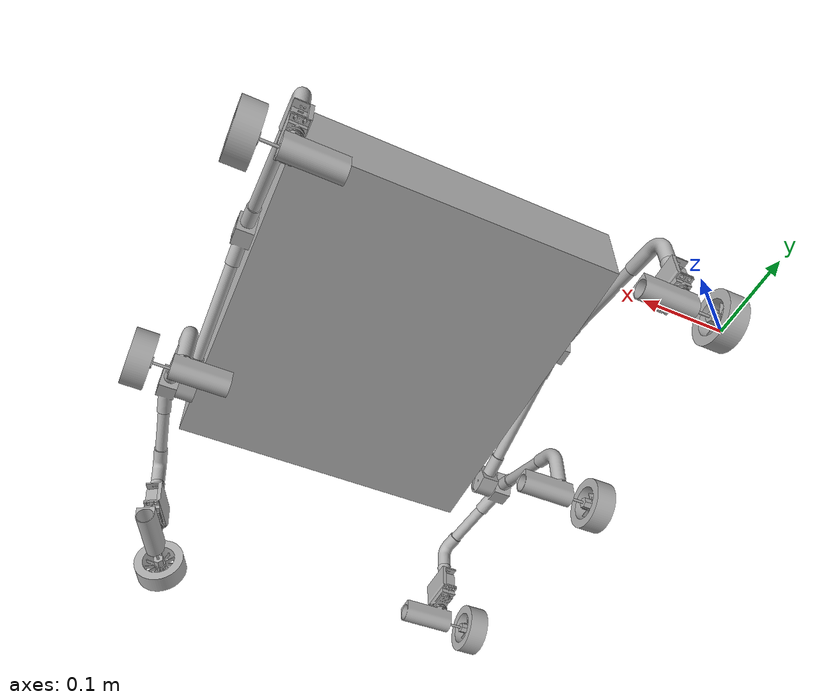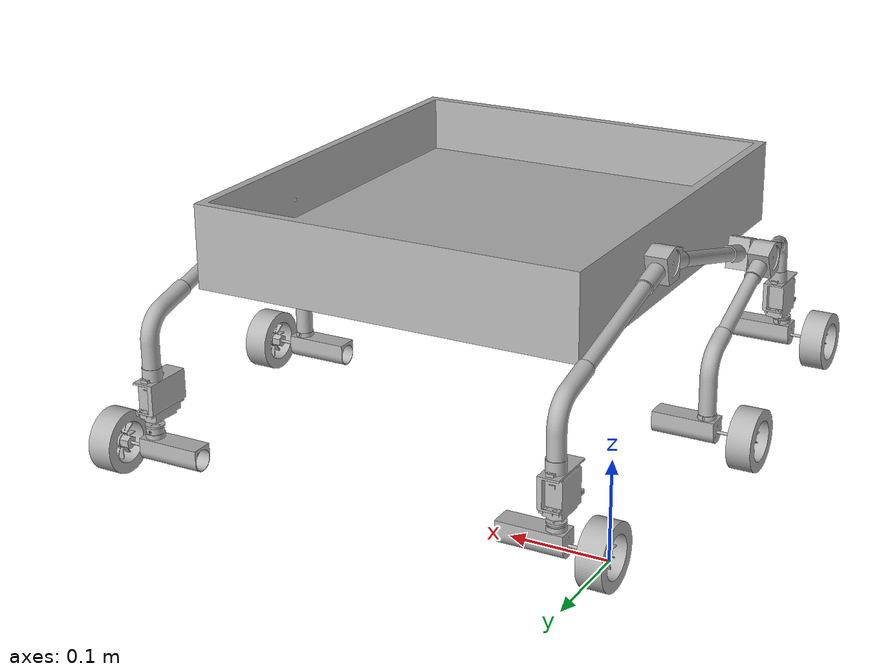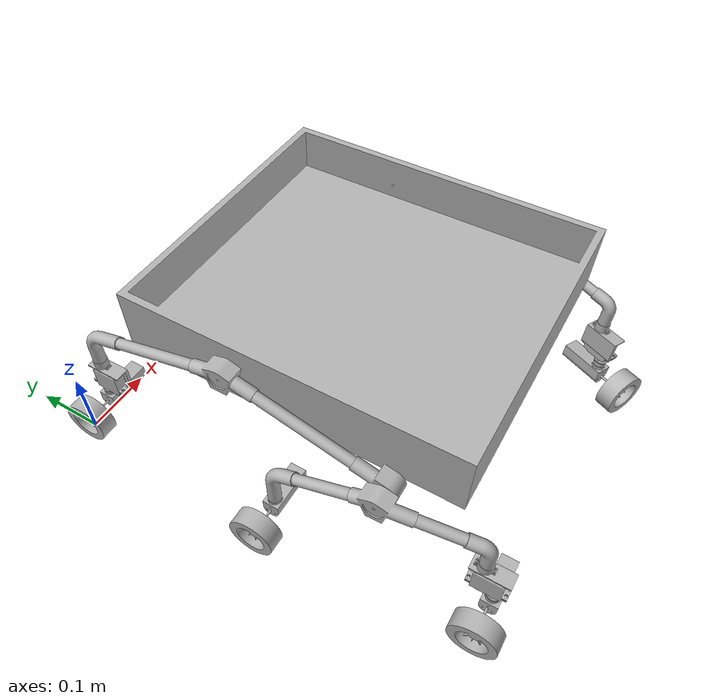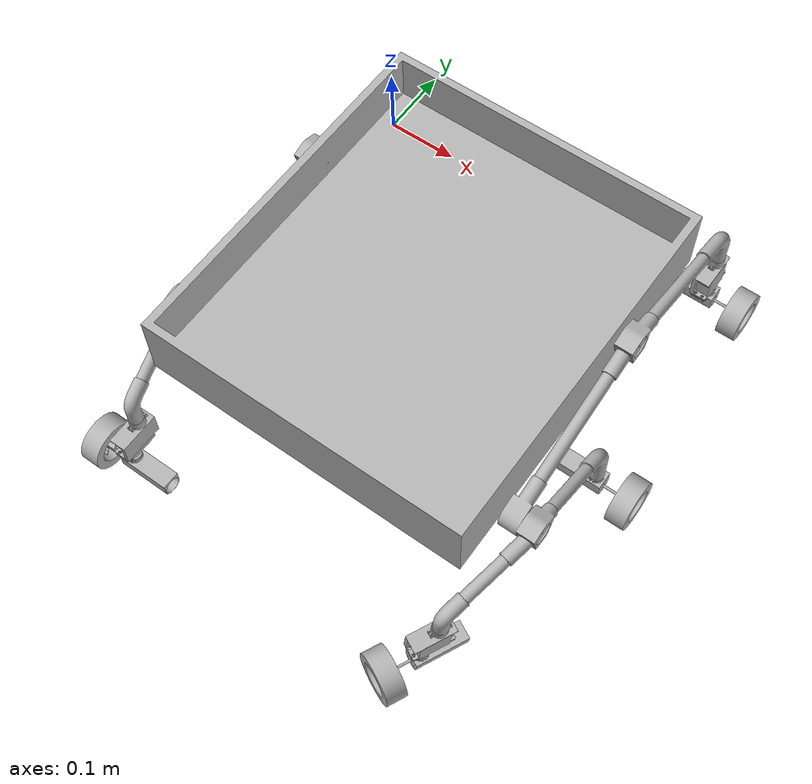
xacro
<?xml version="1.0" ?>
<robot name="Final" xmlns:xacro="http://www.ros.org/wiki/xacro">

<xacro:include filename="$(find Final_description)/urdf/materials.xacro" />
<xacro:include filename="$(find Final_description)/urdf/Final.trans" />
<xacro:include filename="$(find Final_description)/urdf/Final.gazebo" />
<link name="base_link">
  <inertial>
    <origin xyz="0.27479476929251384 -0.30008200371305216 0.17667763447374185" rpy="0 0 0"/>
    <mass value="55.913914162590295"/>
    <inertia ixx="1.217494" iyy="0.976224" izz="2.152979" ixy="-0.0" iyz="3e-06" ixz="-0.0"/>
  </inertial>
  <visual>
    <origin xyz="0 0 0" rpy="0 0 0"/>
    <geometry>
      <mesh filename="file://$(find Final_description)/meshes/base_link.stl" scale="0.001 0.001 0.001"/>
    </geometry>
    <material name="silver"/>
  </visual>
  <collision>
    <origin xyz="0 0 0" rpy="0 0 0"/>
    <geometry>
      <mesh filename="file://$(find Final_description)/meshes/base_link.stl" scale="0.001 0.001 0.001"/>
    </geometry>
  </collision>
</link>

<link name="pipe_lower_middle_left_1">
  <inertial>
    <origin xyz="-8.977955739952748e-10 0.04003407451151508 -0.01734773251751537" rpy="0 0 0"/>
    <mass value="0.04519259365656495"/>
    <inertia ixx="3e-05" iyy="7e-06" izz="2.5e-05" ixy="0.0" iyz="1e-05" ixz="-0.0"/>
  </inertial>
  <visual>
    <origin xyz="-0.027 0.416472 -0.130474" rpy="0 0 0"/>
    <geometry>
      <mesh filename="file://$(find Final_description)/meshes/pipe_lower_middle_left_1.stl" scale="0.001 0.001 0.001"/>
    </geometry>
    <material name="silver"/>
  </visual>
  <collision>
    <origin xyz="-0.027 0.416472 -0.130474" rpy="0 0 0"/>
    <geometry>
      <mesh filename="file://$(find Final_description)/meshes/pipe_lower_middle_left_1.stl" scale="0.001 0.001 0.001"/>
    </geometry>
  </collision>
</link>

<link name="pipe_lower_middle_right_1">
  <inertial>
    <origin xyz="-4.605171765037497e-07 0.04003458754758321 -0.017348204771329576" rpy="0 0 0"/>
    <mass value="0.04519259365656495"/>
    <inertia ixx="3e-05" iyy="7e-06" izz="2.5e-05" ixy="-0.0" iyz="1e-05" ixz="0.0"/>
  </inertial>
  <visual>
    <origin xyz="-0.52259 0.416724 -0.129807" rpy="0 0 0"/>
    <geometry>
      <mesh filename="file://$(find Final_description)/meshes/pipe_lower_middle_right_1.stl" scale="0.001 0.001 0.001"/>
    </geometry>
    <material name="silver"/>
  </visual>
  <collision>
    <origin xyz="-0.52259 0.416724 -0.129807" rpy="0 0 0"/>
    <geometry>
      <mesh filename="file://$(find Final_description)/meshes/pipe_lower_middle_right_1.stl" scale="0.001 0.001 0.001"/>
    </geometry>
  </collision>
</link>

<link name="pipe_dc_link_left_1">
  <inertial>
    <origin xyz="-8.9779555664804e-10 0.028924035569890205 -0.031485847561033245" rpy="0 0 0"/>
    <mass value="0.06003524287853614"/>
    <inertia ixx="4.3e-05" iyy="3.6e-05" izz="1.1e-05" ixy="0.0" iyz="1.2e-05" ixz="0.0"/>
  </inertial>
  <visual>
    <origin xyz="-0.027 0.336404 -0.095778" rpy="0 0 0"/>
    <geometry>
      <mesh filename="file://$(find Final_description)/meshes/pipe_dc_link_left_1.stl" scale="0.001 0.001 0.001"/>
    </geometry>
    <material name="silver"/>
  </visual>
  <collision>
    <origin xyz="-0.027 0.336404 -0.095778" rpy="0 0 0"/>
    <geometry>
      <mesh filename="file://$(find Final_description)/meshes/pipe_dc_link_left_1.stl" scale="0.001 0.001 0.001"/>
    </geometry>
  </collision>
</link>

<link name="pipe_dc_link_right_1">
  <inertial>
    <origin xyz="-4.605171771698835e-07 0.02892354860595492 -0.031486319814844704" rpy="0 0 0"/>
    <mass value="0.06003524287853614"/>
    <inertia ixx="4.3e-05" iyy="3.6e-05" izz="1.1e-05" ixy="0.0" iyz="1.2e-05" ixz="0.0"/>
  </inertial>
  <visual>
    <origin xyz="-0.52259 0.336655 -0.095111" rpy="0 0 0"/>
    <geometry>
      <mesh filename="file://$(find Final_description)/meshes/pipe_dc_link_right_1.stl" scale="0.001 0.001 0.001"/>
    </geometry>
    <material name="silver"/>
  </visual>
  <collision>
    <origin xyz="-0.52259 0.336655 -0.095111" rpy="0 0 0"/>
    <geometry>
      <mesh filename="file://$(find Final_description)/meshes/pipe_dc_link_right_1.stl" scale="0.001 0.001 0.001"/>
    </geometry>
  </collision>
</link>

<link name="pipe_rear_left_1">
  <inertial>
    <origin xyz="0.006871785442725348 -0.02905675193777263 -0.006465187833986086" rpy="0 0 0"/>
    <mass value="0.03164317364049532"/>
    <inertia ixx="1e-05" iyy="2e-06" izz="1e-05" ixy="2e-06" iyz="-2e-06" ixz="0.0"/>
  </inertial>
  <visual>
    <origin xyz="-0.033749 0.494601 -0.135058" rpy="0 0 0"/>
    <geometry>
      <mesh filename="file://$(find Final_description)/meshes/pipe_rear_left_1.stl" scale="0.001 0.001 0.001"/>
    </geometry>
    <material name="silver"/>
  </visual>
  <collision>
    <origin xyz="-0.033749 0.494601 -0.135058" rpy="0 0 0"/>
    <geometry>
      <mesh filename="file://$(find Final_description)/meshes/pipe_rear_left_1.stl" scale="0.001 0.001 0.001"/>
    </geometry>
  </collision>
</link>

<link name="pipe_rear_right_1">
  <inertial>
    <origin xyz="-0.006872246857697162 -0.02905623890169773 -0.006464660087800833" rpy="0 0 0"/>
    <mass value="0.03164317364049532"/>
    <inertia ixx="1e-05" iyy="2e-06" izz="1e-05" ixy="-2e-06" iyz="-2e-06" ixz="-0.0"/>
  </inertial>
  <visual>
    <origin xyz="-0.515841 0.494853 -0.13439" rpy="0 0 0"/>
    <geometry>
      <mesh filename="file://$(find Final_description)/meshes/pipe_rear_right_1.stl" scale="0.001 0.001 0.001"/>
    </geometry>
    <material name="silver"/>
  </visual>
  <collision>
    <origin xyz="-0.515841 0.494853 -0.13439" rpy="0 0 0"/>
    <geometry>
      <mesh filename="file://$(find Final_description)/meshes/pipe_rear_right_1.stl" scale="0.001 0.001 0.001"/>
    </geometry>
  </collision>
</link>

<link name="pipe_front_left_1">
  <inertial>
    <origin xyz="-8.977956503231077e-10 0.06443531685701423 -0.017265117510889577" rpy="0 0 0"/>
    <mass value="0.06909570818320863"/>
    <inertia ixx="0.000104" iyy="1e-05" izz="9.7e-05" ixy="0.0" iyz="2.5e-05" ixz="0.0"/>
  </inertial>
  <visual>
    <origin xyz="-0.051 0.180065 -0.193248" rpy="0 0 0"/>
    <geometry>
      <mesh filename="file://$(find Final_description)/meshes/pipe_front_left_1.stl" scale="0.001 0.001 0.001"/>
    </geometry>
    <material name="silver"/>
  </visual>
  <collision>
    <origin xyz="-0.051 0.180065 -0.193248" rpy="0 0 0"/>
    <geometry>
      <mesh filename="file://$(find Final_description)/meshes/pipe_front_left_1.stl" scale="0.001 0.001 0.001"/>
    </geometry>
  </collision>
</link>

<link name="pipe_servo_link_left_1">
  <inertial>
    <origin xyz="-8.977956572620016e-10 0.04244429431367434 -0.027430891810267533" rpy="0 0 0"/>
    <mass value="0.07120694035150302"/>
    <inertia ixx="6.6e-05" iyy="4.2e-05" izz="2.9e-05" ixy="0.0" iyz="2.4e-05" ixz="0.0"/>
  </inertial>
  <visual>
    <origin xyz="-0.051 0.051194 -0.158717" rpy="0 0 0"/>
    <geometry>
      <mesh filename="file://$(find Final_description)/meshes/pipe_servo_link_left_1.stl" scale="0.001 0.001 0.001"/>
    </geometry>
    <material name="silver"/>
  </visual>
  <collision>
    <origin xyz="-0.051 0.051194 -0.158717" rpy="0 0 0"/>
    <geometry>
      <mesh filename="file://$(find Final_description)/meshes/pipe_servo_link_left_1.stl" scale="0.001 0.001 0.001"/>
    </geometry>
  </collision>
</link>

<link name="pipe_front_right_1">
  <inertial>
    <origin xyz="-4.605171760041493e-07 0.06443582989306776 -0.017265589764707323" rpy="0 0 0"/>
    <mass value="0.06909570818320863"/>
    <inertia ixx="0.000104" iyy="1e-05" izz="9.7e-05" ixy="0.0" iyz="2.5e-05" ixz="0.0"/>
  </inertial>
  <visual>
    <origin xyz="-0.49859 0.180317 -0.192581" rpy="0 0 0"/>
    <geometry>
      <mesh filename="file://$(find Final_description)/meshes/pipe_front_right_1.stl" scale="0.001 0.001 0.001"/>
    </geometry>
    <material name="silver"/>
  </visual>
  <collision>
    <origin xyz="-0.49859 0.180317 -0.192581" rpy="0 0 0"/>
    <geometry>
      <mesh filename="file://$(find Final_description)/meshes/pipe_front_right_1.stl" scale="0.001 0.001 0.001"/>
    </geometry>
  </collision>
</link>

<link name="pipe_servo_link_right_1">
  <inertial>
    <origin xyz="-4.605171760041493e-07 0.04244480734972258 -0.027431364064083058" rpy="0 0 0"/>
    <mass value="0.07120694035150302"/>
    <inertia ixx="6.6e-05" iyy="4.2e-05" izz="2.9e-05" ixy="0.0" iyz="2.4e-05" ixz="0.0"/>
  </inertial>
  <visual>
    <origin xyz="-0.49859 0.051446 -0.15805" rpy="0 0 0"/>
    <geometry>
      <mesh filename="file://$(find Final_description)/meshes/pipe_servo_link_right_1.stl" scale="0.001 0.001 0.001"/>
    </geometry>
    <material name="silver"/>
  </visual>
  <collision>
    <origin xyz="-0.49859 0.051446 -0.15805" rpy="0 0 0"/>
    <geometry>
      <mesh filename="file://$(find Final_description)/meshes/pipe_servo_link_right_1.stl" scale="0.001 0.001 0.001"/>
    </geometry>
  </collision>
</link>

<link name="pipe_servo_link_rear_right_1">
  <inertial>
    <origin xyz="0.005355259210536749 -0.02265939313426768 -0.018085634757808167" rpy="0 0 0"/>
    <mass value="0.0434992669495612"/>
    <inertia ixx="1.6e-05" iyy="1.3e-05" izz="6e-06" ixy="1e-06" iyz="-4e-06" ixz="1e-06"/>
  </inertial>
  <visual>
    <origin xyz="-0.047493 0.552714 -0.122128" rpy="0 0 0"/>
    <geometry>
      <mesh filename="file://$(find Final_description)/meshes/pipe_servo_link_rear_right_1.stl" scale="0.001 0.001 0.001"/>
    </geometry>
    <material name="silver"/>
  </visual>
  <collision>
    <origin xyz="-0.047493 0.552714 -0.122128" rpy="0 0 0"/>
    <geometry>
      <mesh filename="file://$(find Final_description)/meshes/pipe_servo_link_rear_right_1.stl" scale="0.001 0.001 0.001"/>
    </geometry>
  </collision>
</link>

<link name="pipe_servo_link_rear_right__1__1">
  <inertial>
    <origin xyz="-0.006604154062734735 -0.02237731083078509 -0.018022459503967928" rpy="0 0 0"/>
    <mass value="0.0434992669495612"/>
    <inertia ixx="1.6e-05" iyy="1.3e-05" izz="6e-06" ixy="-1e-06" iyz="-4e-06" ixz="-2e-06"/>
  </inertial>
  <visual>
    <origin xyz="-0.502096 0.552966 -0.12146" rpy="0 0 0"/>
    <geometry>
      <mesh filename="file://$(find Final_description)/meshes/pipe_servo_link_rear_right__1__1.stl" scale="0.001 0.001 0.001"/>
    </geometry>
    <material name="silver"/>
  </visual>
  <collision>
    <origin xyz="-0.502096 0.552966 -0.12146" rpy="0 0 0"/>
    <geometry>
      <mesh filename="file://$(find Final_description)/meshes/pipe_servo_link_rear_right__1__1.stl" scale="0.001 0.001 0.001"/>
    </geometry>
  </collision>
</link>

<link name="pipe_joint_front_right_1">
  <inertial>
    <origin xyz="0.011999539482823951 -3.4385035208028825e-07 -0.0024021453067086806" rpy="0 0 0"/>
    <mass value="0.22220705254181228"/>
    <inertia ixx="7.5e-05" iyy="3e-05" izz="6.4e-05" ixy="-0.0" iyz="-0.0" ixz="0.0"/>
  </inertial>
  <visual>
    <origin xyz="-0.48659 0.225232 -0.204616" rpy="0 0 0"/>
    <geometry>
      <mesh filename="file://$(find Final_description)/meshes/pipe_joint_front_right_1.stl" scale="0.001 0.001 0.001"/>
    </geometry>
    <material name="silver"/>
  </visual>
  <collision>
    <origin xyz="-0.48659 0.225232 -0.204616" rpy="0 0 0"/>
    <geometry>
      <mesh filename="file://$(find Final_description)/meshes/pipe_joint_front_right_1.stl" scale="0.001 0.001 0.001"/>
    </geometry>
  </collision>
</link>

<link name="pipe_joint_front_1">
  <inertial>
    <origin xyz="-0.012000000897795647 1.4311358853547063e-07 -0.0024016730528896024" rpy="0 0 0"/>
    <mass value="0.22220705254181228"/>
    <inertia ixx="7.5e-05" iyy="3e-05" izz="6.4e-05" ixy="0.0" iyz="-0.0" ixz="0.0"/>
  </inertial>
  <visual>
    <origin xyz="-0.063 0.224981 -0.205283" rpy="0 0 0"/>
    <geometry>
      <mesh filename="file://$(find Final_description)/meshes/pipe_joint_front_1.stl" scale="0.001 0.001 0.001"/>
    </geometry>
    <material name="silver"/>
  </visual>
  <collision>
    <origin xyz="-0.063 0.224981 -0.205283" rpy="0 0 0"/>
    <geometry>
      <mesh filename="file://$(find Final_description)/meshes/pipe_joint_front_1.stl" scale="0.001 0.001 0.001"/>
    </geometry>
  </collision>
</link>

<link name="link_servo_pipe_left_1_1">
  <inertial>
    <origin xyz="1.804210421202379e-07 1.5952948503317188e-06 0.0014266508339962763" rpy="0 0 0"/>
    <mass value="0.015201508636835502"/>
    <inertia ixx="1e-06" iyy="1e-06" izz="1e-06" ixy="-0.0" iyz="0.0" ixz="0.0"/>
  </inertial>
  <visual>
    <origin xyz="-0.054236 0.58128 -0.072779" rpy="0 0 0"/>
    <geometry>
      <mesh filename="file://$(find Final_description)/meshes/link_servo_pipe_left_1_1.stl" scale="0.001 0.001 0.001"/>
    </geometry>
    <material name="silver"/>
  </visual>
  <collision>
    <origin xyz="-0.054236 0.58128 -0.072779" rpy="0 0 0"/>
    <geometry>
      <mesh filename="file://$(find Final_description)/meshes/link_servo_pipe_left_1_1.stl" scale="0.001 0.001 0.001"/>
    </geometry>
  </collision>
</link>

<link name="link_servo_pipe_v1__1__1">
  <inertial>
    <origin xyz="0.00013684019224452504 -2.962650466975525e-05 0.001419814807434444" rpy="0 0 0"/>
    <mass value="0.015201508636835502"/>
    <inertia ixx="1e-06" iyy="1e-06" izz="1e-06" ixy="-0.0" iyz="-0.0" ixz="0.0"/>
  </inertial>
  <visual>
    <origin xyz="-0.491235 0.580603 -0.072318" rpy="0 0 0"/>
    <geometry>
      <mesh filename="file://$(find Final_description)/meshes/link_servo_pipe_v1__1__1.stl" scale="0.001 0.001 0.001"/>
    </geometry>
    <material name="silver"/>
  </visual>
  <collision>
    <origin xyz="-0.491235 0.580603 -0.072318" rpy="0 0 0"/>
    <geometry>
      <mesh filename="file://$(find Final_description)/meshes/link_servo_pipe_v1__1__1.stl" scale="0.001 0.001 0.001"/>
    </geometry>
  </collision>
</link>

<link name="MG995_servo_bracket__Mirror__v1__1__1">
  <inertial>
    <origin xyz="-0.003944241793205405 0.003165022569346032 -0.01246363603343284" rpy="0 0 0"/>
    <mass value="0.057318375547853934"/>
    <inertia ixx="2.2e-05" iyy="1.2e-05" izz="2e-05" ixy="-6e-06" iyz="1e-06" ixz="-2e-06"/>
  </inertial>
  <visual>
    <origin xyz="-0.484225 0.590072 -0.069779" rpy="0 0 0"/>
    <geometry>
      <mesh filename="file://$(find Final_description)/meshes/MG995_servo_bracket__Mirror__v1__1__1.stl" scale="0.001 0.001 0.001"/>
    </geometry>
    <material name="silver"/>
  </visual>
  <collision>
    <origin xyz="-0.484225 0.590072 -0.069779" rpy="0 0 0"/>
    <geometry>
      <mesh filename="file://$(find Final_description)/meshes/MG995_servo_bracket__Mirror__v1__1__1.stl" scale="0.001 0.001 0.001"/>
    </geometry>
  </collision>
</link>

<link name="link_servo_pipe_v1__2__1">
  <inertial>
    <origin xyz="-4.6750606935708205e-07 4.5041052804985215e-08 0.0014260293122546758" rpy="0 0 0"/>
    <mass value="0.015201508636835502"/>
    <inertia ixx="1e-06" iyy="1e-06" izz="1e-06" ixy="0.0" iyz="0.0" ixz="-0.0"/>
  </inertial>
  <visual>
    <origin xyz="-0.49859 -0.00651 -0.082521" rpy="0 0 0"/>
    <geometry>
      <mesh filename="file://$(find Final_description)/meshes/link_servo_pipe_v1__2__1.stl" scale="0.001 0.001 0.001"/>
    </geometry>
    <material name="silver"/>
  </visual>
  <collision>
    <origin xyz="-0.49859 -0.00651 -0.082521" rpy="0 0 0"/>
    <geometry>
      <mesh filename="file://$(find Final_description)/meshes/link_servo_pipe_v1__2__1.stl" scale="0.001 0.001 0.001"/>
    </geometry>
  </collision>
</link>

<link name="MG995_servo_bracket__Mirror__v1_1">
  <inertial>
    <origin xyz="-0.0037126238101324316 -0.02155371380073145 -0.012847549764952546" rpy="0 0 0"/>
    <mass value="0.057318375547853934"/>
    <inertia ixx="2.5e-05" iyy="9e-06" izz="2e-05" ixy="0.0" iyz="0.0" ixz="-1e-06"/>
  </inertial>
  <visual>
    <origin xyz="-0.49659 -0.01801 -0.079521" rpy="0 0 0"/>
    <geometry>
      <mesh filename="file://$(find Final_description)/meshes/MG995_servo_bracket__Mirror__v1_1.stl" scale="0.001 0.001 0.001"/>
    </geometry>
    <material name="silver"/>
  </visual>
  <collision>
    <origin xyz="-0.49659 -0.01801 -0.079521" rpy="0 0 0"/>
    <geometry>
      <mesh filename="file://$(find Final_description)/meshes/MG995_servo_bracket__Mirror__v1_1.stl" scale="0.001 0.001 0.001"/>
    </geometry>
  </collision>
</link>

<link name="link_servo_pipe_v1__3__1">
  <inertial>
    <origin xyz="-7.88668901713363e-09 5.320050052931916e-07 0.0014265015660680919" rpy="0 0 0"/>
    <mass value="0.015201508636835502"/>
    <inertia ixx="1e-06" iyy="1e-06" izz="1e-06" ixy="0.0" iyz="0.0" ixz="-0.0"/>
  </inertial>
  <visual>
    <origin xyz="-0.051 -0.006761 -0.083188" rpy="0 0 0"/>
    <geometry>
      <mesh filename="file://$(find Final_description)/meshes/link_servo_pipe_v1__3__1.stl" scale="0.001 0.001 0.001"/>
    </geometry>
    <material name="silver"/>
  </visual>
  <collision>
    <origin xyz="-0.051 -0.006761 -0.083188" rpy="0 0 0"/>
    <geometry>
      <mesh filename="file://$(find Final_description)/meshes/link_servo_pipe_v1__3__1.stl" scale="0.001 0.001 0.001"/>
    </geometry>
  </collision>
</link>

<link name="MG995_servo_bracket_v1_1">
  <inertial>
    <origin xyz="0.007712164098406825 -0.021553227063067917 -0.012847077491676837" rpy="0 0 0"/>
    <mass value="0.05731837512876885"/>
    <inertia ixx="2.5e-05" iyy="9e-06" izz="2e-05" ixy="-0.0" iyz="0.0" ixz="1e-06"/>
  </inertial>
  <visual>
    <origin xyz="-0.049 -0.018261 -0.080188" rpy="0 0 0"/>
    <geometry>
      <mesh filename="file://$(find Final_description)/meshes/MG995_servo_bracket_v1_1.stl" scale="0.001 0.001 0.001"/>
    </geometry>
    <material name="silver"/>
  </visual>
  <collision>
    <origin xyz="-0.049 -0.018261 -0.080188" rpy="0 0 0"/>
    <geometry>
      <mesh filename="file://$(find Final_description)/meshes/MG995_servo_bracket_v1_1.stl" scale="0.001 0.001 0.001"/>
    </geometry>
  </collision>
</link>

<link name="MG995_servo_bracket_v1__1__1">
  <inertial>
    <origin xyz="0.003698281640410757 -0.021564938986444737 -0.012832205935074163" rpy="0 0 0"/>
    <mass value="0.05731837512876885"/>
    <inertia ixx="2.5e-05" iyy="9e-06" izz="2e-05" ixy="-0.0" iyz="0.0" ixz="1e-06"/>
  </inertial>
  <visual>
    <origin xyz="-0.056242 0.569783 -0.069771" rpy="0 0 0"/>
    <geometry>
      <mesh filename="file://$(find Final_description)/meshes/MG995_servo_bracket_v1__1__1.stl" scale="0.001 0.001 0.001"/>
    </geometry>
    <material name="silver"/>
  </visual>
  <collision>
    <origin xyz="-0.056242 0.569783 -0.069771" rpy="0 0 0"/>
    <geometry>
      <mesh filename="file://$(find Final_description)/meshes/MG995_servo_bracket_v1__1__1.stl" scale="0.001 0.001 0.001"/>
    </geometry>
  </collision>
</link>

<link name="MG995_servo_v1__3__1">
  <inertial>
    <origin xyz="0.004849992372636981 -0.023834124788538986 0.009115742556435436" rpy="0 0 0"/>
    <mass value="0.2546936082010987"/>
    <inertia ixx="6.9e-05" iyy="4.2e-05" izz="4.3e-05" ixy="-0.0" iyz="1e-06" ixz="-0.0"/>
  </inertial>
  <visual>
    <origin xyz="-0.04515 -0.020761 -0.047088" rpy="0 0 0"/>
    <geometry>
      <mesh filename="file://$(find Final_description)/meshes/MG995_servo_v1__3__1.stl" scale="0.001 0.001 0.001"/>
    </geometry>
    <material name="silver"/>
  </visual>
  <collision>
    <origin xyz="-0.04515 -0.020761 -0.047088" rpy="0 0 0"/>
    <geometry>
      <mesh filename="file://$(find Final_description)/meshes/MG995_servo_v1__3__1.stl" scale="0.001 0.001 0.001"/>
    </geometry>
  </collision>
</link>

<link name="MG995_servo_v1__2__1">
  <inertial>
    <origin xyz="0.004837618757672864 -0.024161655237159296 0.009132567012130485" rpy="0 0 0"/>
    <mass value="0.2546936082010987"/>
    <inertia ixx="6.9e-05" iyy="4.2e-05" izz="4.3e-05" ixy="-0.0" iyz="-1e-06" ixz="-0.0"/>
  </inertial>
  <visual>
    <origin xyz="-0.048389 0.567303 -0.03667" rpy="0 0 0"/>
    <geometry>
      <mesh filename="file://$(find Final_description)/meshes/MG995_servo_v1__2__1.stl" scale="0.001 0.001 0.001"/>
    </geometry>
    <material name="silver"/>
  </visual>
  <collision>
    <origin xyz="-0.048389 0.567303 -0.03667" rpy="0 0 0"/>
    <geometry>
      <mesh filename="file://$(find Final_description)/meshes/MG995_servo_v1__2__1.stl" scale="0.001 0.001 0.001"/>
    </geometry>
  </collision>
</link>

<link name="MG995_servo_v1_1">
  <inertial>
    <origin xyz="0.0048495326191461685 -0.023834611752491585 0.00911527030262197" rpy="0 0 0"/>
    <mass value="0.2546936082010987"/>
    <inertia ixx="6.9e-05" iyy="4.2e-05" izz="4.3e-05" ixy="-0.0" iyz="1e-06" ixz="-0.0"/>
  </inertial>
  <visual>
    <origin xyz="-0.49474 -0.02051 -0.046421" rpy="0 0 0"/>
    <geometry>
      <mesh filename="file://$(find Final_description)/meshes/MG995_servo_v1_1.stl" scale="0.001 0.001 0.001"/>
    </geometry>
    <material name="silver"/>
  </visual>
  <collision>
    <origin xyz="-0.49474 -0.02051 -0.046421" rpy="0 0 0"/>
    <geometry>
      <mesh filename="file://$(find Final_description)/meshes/MG995_servo_v1_1.stl" scale="0.001 0.001 0.001"/>
    </geometry>
  </collision>
</link>

<link name="MG995_servo_v1__1__1">
  <inertial>
    <origin xyz="0.006723574592660819 0.023417952027181443 0.009003343596641858" rpy="0 0 0"/>
    <mass value="0.2546936082010987"/>
    <inertia ixx="6.4e-05" iyy="4.7e-05" izz="4.4e-05" ixy="-1e-05" iyz="0.0" ixz="-2e-06"/>
  </inertial>
  <visual>
    <origin xyz="-0.478475 0.61307 -0.036591" rpy="0 0 0"/>
    <geometry>
      <mesh filename="file://$(find Final_description)/meshes/MG995_servo_v1__1__1.stl" scale="0.001 0.001 0.001"/>
    </geometry>
    <material name="silver"/>
  </visual>
  <collision>
    <origin xyz="-0.478475 0.61307 -0.036591" rpy="0 0 0"/>
    <geometry>
      <mesh filename="file://$(find Final_description)/meshes/MG995_servo_v1__1__1.stl" scale="0.001 0.001 0.001"/>
    </geometry>
  </collision>
</link>

<link name="servo_connector_v2__3__1">
  <inertial>
    <origin xyz="-2.1510571102112408e-15 1.4745069269999495e-07 -0.003976447469667691" rpy="0 0 0"/>
    <mass value="0.0046864154109674235"/>
    <inertia ixx="0.0" iyy="0.0" izz="0.0" ixy="0.0" iyz="-0.0" ixz="0.0"/>
  </inertial>
  <visual>
    <origin xyz="-0.05 -0.006761 -0.035188" rpy="0 0 0"/>
    <geometry>
      <mesh filename="file://$(find Final_description)/meshes/servo_connector_v2__3__1.stl" scale="0.001 0.001 0.001"/>
    </geometry>
    <material name="silver"/>
  </visual>
  <collision>
    <origin xyz="-0.05 -0.006761 -0.035188" rpy="0 0 0"/>
    <geometry>
      <mesh filename="file://$(find Final_description)/meshes/servo_connector_v2__3__1.stl" scale="0.001 0.001 0.001"/>
    </geometry>
  </collision>
</link>

<link name="servo_connector_v2__2__1">
  <inertial>
    <origin xyz="-0.000380290424029206 8.317624563047854e-05 -0.003958025900761757" rpy="0 0 0"/>
    <mass value="0.0046864154109674235"/>
    <inertia ixx="0.0" iyy="0.0" izz="0.0" ixy="-0.0" iyz="-0.0" ixz="0.0"/>
  </inertial>
  <visual>
    <origin xyz="-0.478976 0.598098 -0.024899" rpy="0 0 0"/>
    <geometry>
      <mesh filename="file://$(find Final_description)/meshes/servo_connector_v2__2__1.stl" scale="0.001 0.001 0.001"/>
    </geometry>
    <material name="silver"/>
  </visual>
  <collision>
    <origin xyz="-0.478976 0.598098 -0.024899" rpy="0 0 0"/>
    <geometry>
      <mesh filename="file://$(find Final_description)/meshes/servo_connector_v2__2__1.stl" scale="0.001 0.001 0.001"/>
    </geometry>
  </collision>
</link>

<link name="servo_connector_v2_1">
  <inertial>
    <origin xyz="-4.597534928318936e-07 -3.395132598966316e-07 -0.003976919723481152" rpy="0 0 0"/>
    <mass value="0.0046864154109674235"/>
    <inertia ixx="0.0" iyy="0.0" izz="0.0" ixy="0.0" iyz="-0.0" ixz="0.0"/>
  </inertial>
  <visual>
    <origin xyz="-0.49959 -0.00651 -0.033521" rpy="0 0 0"/>
    <geometry>
      <mesh filename="file://$(find Final_description)/meshes/servo_connector_v2_1.stl" scale="0.001 0.001 0.001"/>
    </geometry>
    <material name="silver"/>
  </visual>
  <collision>
    <origin xyz="-0.49959 -0.00651 -0.033521" rpy="0 0 0"/>
    <geometry>
      <mesh filename="file://$(find Final_description)/meshes/servo_connector_v2_1.stl" scale="0.001 0.001 0.001"/>
    </geometry>
  </collision>
</link>

<link name="servo_connector_v2__1__1">
  <inertial>
    <origin xyz="-4.598270128969295e-07 -3.194729292554932e-06 -0.003976323402976035" rpy="0 0 0"/>
    <mass value="0.0046864154109674235"/>
    <inertia ixx="0.0" iyy="0.0" izz="0.0" ixy="0.0" iyz="0.0" ixz="0.0"/>
  </inertial>
  <visual>
    <origin xyz="-0.053218 0.601315 -0.023794" rpy="0 0 0"/>
    <geometry>
      <mesh filename="file://$(find Final_description)/meshes/servo_connector_v2__1__1.stl" scale="0.001 0.001 0.001"/>
    </geometry>
    <material name="silver"/>
  </visual>
  <collision>
    <origin xyz="-0.053218 0.601315 -0.023794" rpy="0 0 0"/>
    <geometry>
      <mesh filename="file://$(find Final_description)/meshes/servo_connector_v2__1__1.stl" scale="0.001 0.001 0.001"/>
    </geometry>
  </collision>
</link>

<link name="dc_servo_connector_v1__1__1">
  <inertial>
    <origin xyz="-4.5975348983429143e-07 -0.0058670061799167075 -0.0023782267065725685" rpy="0 0 0"/>
    <mass value="0.005700427049502312"/>
    <inertia ixx="0.0" iyy="0.0" izz="0.0" ixy="0.0" iyz="-0.0" ixz="0.0"/>
  </inertial>
  <visual>
    <origin xyz="-0.49959 -0.012377 -0.028521" rpy="0 0 0"/>
    <geometry>
      <mesh filename="file://$(find Final_description)/meshes/dc_servo_connector_v1__1__1.stl" scale="0.001 0.001 0.001"/>
    </geometry>
    <material name="silver"/>
  </visual>
  <collision>
    <origin xyz="-0.49959 -0.012377 -0.028521" rpy="0 0 0"/>
    <geometry>
      <mesh filename="file://$(find Final_description)/meshes/dc_servo_connector_v1__1__1.stl" scale="0.001 0.001 0.001"/>
    </geometry>
  </collision>
</link>

<link name="dc_servo_connector_v1__3__1">
  <inertial>
    <origin xyz="8.049116928532385e-16 -0.005866519215964102 -0.002377754452759097" rpy="0 0 0"/>
    <mass value="0.005700427049502312"/>
    <inertia ixx="0.0" iyy="0.0" izz="0.0" ixy="0.0" iyz="-0.0" ixz="-0.0"/>
  </inertial>
  <visual>
    <origin xyz="-0.05 -0.012628 -0.030188" rpy="0 0 0"/>
    <geometry>
      <mesh filename="file://$(find Final_description)/meshes/dc_servo_connector_v1__3__1.stl" scale="0.001 0.001 0.001"/>
    </geometry>
    <material name="silver"/>
  </visual>
  <collision>
    <origin xyz="-0.05 -0.012628 -0.030188" rpy="0 0 0"/>
    <geometry>
      <mesh filename="file://$(find Final_description)/meshes/dc_servo_connector_v1__3__1.stl" scale="0.001 0.001 0.001"/>
    </geometry>
  </collision>
</link>

<link name="dc_servo_connector_v1__2__1">
  <inertial>
    <origin xyz="3.0994616557131205e-06 0.005864950076914344 -0.002382629175466694" rpy="0 0 0"/>
    <mass value="0.005700427049502312"/>
    <inertia ixx="0.0" iyy="0.0" izz="0.0" ixy="0.0" iyz="0.0" ixz="0.0"/>
  </inertial>
  <visual>
    <origin xyz="-0.053214 0.607186 -0.018799" rpy="0 0 0"/>
    <geometry>
      <mesh filename="file://$(find Final_description)/meshes/dc_servo_connector_v1__2__1.stl" scale="0.001 0.001 0.001"/>
    </geometry>
    <material name="silver"/>
  </visual>
  <collision>
    <origin xyz="-0.053214 0.607186 -0.018799" rpy="0 0 0"/>
    <geometry>
      <mesh filename="file://$(find Final_description)/meshes/dc_servo_connector_v1__2__1.stl" scale="0.001 0.001 0.001"/>
    </geometry>
  </collision>
</link>

<link name="dc_servo_connector_v1_1">
  <inertial>
    <origin xyz="0.002285263847305319 0.005348762023907994 -0.002496991488465175" rpy="0 0 0"/>
    <mass value="0.005700427049502312"/>
    <inertia ixx="0.0" iyy="0.0" izz="0.0" ixy="0.0" iyz="-0.0" ixz="0.0"/>
  </inertial>
  <visual>
    <origin xyz="-0.475985 0.603293 -0.020053" rpy="0 0 0"/>
    <geometry>
      <mesh filename="file://$(find Final_description)/meshes/dc_servo_connector_v1_1.stl" scale="0.001 0.001 0.001"/>
    </geometry>
    <material name="silver"/>
  </visual>
  <collision>
    <origin xyz="-0.475985 0.603293 -0.020053" rpy="0 0 0"/>
    <geometry>
      <mesh filename="file://$(find Final_description)/meshes/dc_servo_connector_v1_1.stl" scale="0.001 0.001 0.001"/>
    </geometry>
  </collision>
</link>

<link name="dc_motor_mount_v7__5__1">
  <inertial>
    <origin xyz="0.020178703335684167 4.809577315318531e-07 -0.007499889647916577" rpy="0 0 0"/>
    <mass value="0.10706103527559228"/>
    <inertia ixx="1.4e-05" iyy="5.3e-05" izz="5.4e-05" ixy="-0.0" iyz="-0.0" ixz="-1e-06"/>
  </inertial>
  <visual>
    <origin xyz="-0.05 -0.006761 -0.023188" rpy="0 0 0"/>
    <geometry>
      <mesh filename="file://$(find Final_description)/meshes/dc_motor_mount_v7__5__1.stl" scale="0.001 0.001 0.001"/>
    </geometry>
    <material name="silver"/>
  </visual>
  <collision>
    <origin xyz="-0.05 -0.006761 -0.023188" rpy="0 0 0"/>
    <geometry>
      <mesh filename="file://$(find Final_description)/meshes/dc_motor_mount_v7__5__1.stl" scale="0.001 0.001 0.001"/>
    </geometry>
  </collision>
</link>

<link name="dc_motor_mount_v7_1">
  <inertial>
    <origin xyz="0.020212985560993314 4.2344603051747143e-07 -0.012517319088817525" rpy="0 0 0"/>
    <mass value="0.10687944970522446"/>
    <inertia ixx="1.4e-05" iyy="5.3e-05" izz="5.4e-05" ixy="-0.0" iyz="0.0" ixz="-1e-06"/>
  </inertial>
  <visual>
    <origin xyz="-0.027 0.299702 -0.019874" rpy="0 0 0"/>
    <geometry>
      <mesh filename="file://$(find Final_description)/meshes/dc_motor_mount_v7_1.stl" scale="0.001 0.001 0.001"/>
    </geometry>
    <material name="silver"/>
  </visual>
  <collision>
    <origin xyz="-0.027 0.299702 -0.019874" rpy="0 0 0"/>
    <geometry>
      <mesh filename="file://$(find Final_description)/meshes/dc_motor_mount_v7_1.stl" scale="0.001 0.001 0.001"/>
    </geometry>
  </collision>
</link>

<link name="dc_motor_mount_v7__1__1">
  <inertial>
    <origin xyz="-0.020213446975966054 3.095164807787043e-08 -0.012516791342626553" rpy="0 0 0"/>
    <mass value="0.10687944970522446"/>
    <inertia ixx="1.4e-05" iyy="5.3e-05" izz="5.4e-05" ixy="-0.0" iyz="-0.0" ixz="1e-06"/>
  </inertial>
  <visual>
    <origin xyz="-0.52259 0.299953 -0.019206" rpy="0 0 0"/>
    <geometry>
      <mesh filename="file://$(find Final_description)/meshes/dc_motor_mount_v7__1__1.stl" scale="0.001 0.001 0.001"/>
    </geometry>
    <material name="silver"/>
  </visual>
  <collision>
    <origin xyz="-0.52259 0.299953 -0.019206" rpy="0 0 0"/>
    <geometry>
      <mesh filename="file://$(find Final_description)/meshes/dc_motor_mount_v7__1__1.stl" scale="0.001 0.001 0.001"/>
    </geometry>
  </collision>
</link>

<link name="dc_motor_mount_1_1">
  <inertial>
    <origin xyz="-0.02017916308917489 -6.353612107788675e-09 -0.012500361901729994" rpy="0 0 0"/>
    <mass value="0.10706103527559228"/>
    <inertia ixx="1.4e-05" iyy="5.3e-05" izz="5.4e-05" ixy="-0.0" iyz="0.0" ixz="1e-06"/>
  </inertial>
  <visual>
    <origin xyz="-0.49959 -0.00651 -0.021521" rpy="0 0 0"/>
    <geometry>
      <mesh filename="file://$(find Final_description)/meshes/dc_motor_mount_1_1.stl" scale="0.001 0.001 0.001"/>
    </geometry>
    <material name="silver"/>
  </visual>
  <collision>
    <origin xyz="-0.49959 -0.00651 -0.021521" rpy="0 0 0"/>
    <geometry>
      <mesh filename="file://$(find Final_description)/meshes/dc_motor_mount_1_1.stl" scale="0.001 0.001 0.001"/>
    </geometry>
  </collision>
</link>

<link name="dc_motor_mount_v7__4__1">
  <inertial>
    <origin xyz="0.0074615084013680555 0.018520039356385687 -0.012906529094047721" rpy="0 0 0"/>
    <mass value="0.10687944970522446"/>
    <inertia ixx="4.6e-05" iyy="2.1e-05" izz="5.4e-05" ixy="-1.5e-05" iyz="0.0" ixz="0.0"/>
  </inertial>
  <visual>
    <origin xyz="-0.477828 0.597848 -0.012956" rpy="0 0 0"/>
    <geometry>
      <mesh filename="file://$(find Final_description)/meshes/dc_motor_mount_v7__4__1.stl" scale="0.001 0.001 0.001"/>
    </geometry>
    <material name="silver"/>
  </visual>
  <collision>
    <origin xyz="-0.477828 0.597848 -0.012956" rpy="0 0 0"/>
    <geometry>
      <mesh filename="file://$(find Final_description)/meshes/dc_motor_mount_v7__4__1.stl" scale="0.001 0.001 0.001"/>
    </geometry>
  </collision>
</link>

<link name="dc_motor_shaft_v1__2__1">
  <inertial>
    <origin xyz="-0.010000000000000016 4.80783867326702e-07 2.6668427652309923e-07" rpy="0 0 0"/>
    <mass value="0.0012824751883901918"/>
    <inertia ixx="0.0" iyy="0.0" izz="0.0" ixy="-0.0" iyz="-0.0" ixz="-0.0"/>
  </inertial>
  <visual>
    <origin xyz="-0.038 -0.006761 -0.009188" rpy="0 0 0"/>
    <geometry>
      <mesh filename="file://$(find Final_description)/meshes/dc_motor_shaft_v1__2__1.stl" scale="0.001 0.001 0.001"/>
    </geometry>
    <material name="silver"/>
  </visual>
  <collision>
    <origin xyz="-0.038 -0.006761 -0.009188" rpy="0 0 0"/>
    <geometry>
      <mesh filename="file://$(find Final_description)/meshes/dc_motor_shaft_v1__2__1.stl" scale="0.001 0.001 0.001"/>
    </geometry>
  </collision>
</link>

<link name="dc_motor_shaft_v1__5__1">
  <inertial>
    <origin xyz="-0.010000000897795552 4.7068063852018227e-07 -1.7273549044090081e-07" rpy="0 0 0"/>
    <mass value="0.0012824751883901918"/>
    <inertia ixx="0.0" iyy="0.0" izz="0.0" ixy="-0.0" iyz="-0.0" ixz="-0.0"/>
  </inertial>
  <visual>
    <origin xyz="-0.015 0.299702 -0.000874" rpy="0 0 0"/>
    <geometry>
      <mesh filename="file://$(find Final_description)/meshes/dc_motor_shaft_v1__5__1.stl" scale="0.001 0.001 0.001"/>
    </geometry>
    <material name="silver"/>
  </visual>
  <collision>
    <origin xyz="-0.015 0.299702 -0.000874" rpy="0 0 0"/>
    <geometry>
      <mesh filename="file://$(find Final_description)/meshes/dc_motor_shaft_v1__5__1.stl" scale="0.001 0.001 0.001"/>
    </geometry>
  </collision>
</link>

<link name="dc_motor_mount_v7__2__1">
  <inertial>
    <origin xyz="0.02021151013223335 -1.7824521785780867e-05 -0.007519360095046915" rpy="0 0 0"/>
    <mass value="0.10687944970522446"/>
    <inertia ixx="1.4e-05" iyy="5.3e-05" izz="5.4e-05" ixy="0.0" iyz="0.0" ixz="-1e-06"/>
  </inertial>
  <visual>
    <origin xyz="-0.053217 0.601324 -0.011794" rpy="0 0 0"/>
    <geometry>
      <mesh filename="file://$(find Final_description)/meshes/dc_motor_mount_v7__2__1.stl" scale="0.001 0.001 0.001"/>
    </geometry>
    <material name="silver"/>
  </visual>
  <collision>
    <origin xyz="-0.053217 0.601324 -0.011794" rpy="0 0 0"/>
    <geometry>
      <mesh filename="file://$(find Final_description)/meshes/dc_motor_mount_v7__2__1.stl" scale="0.001 0.001 0.001"/>
    </geometry>
  </collision>
</link>

<link name="dc_motor_shaft_v1__3__1">
  <inertial>
    <origin xyz="-0.010000308465514127 5.906737505667614e-06 1.2370882238100546e-06" rpy="0 0 0"/>
    <mass value="0.0012824751883901918"/>
    <inertia ixx="0.0" iyy="0.0" izz="0.0" ixy="0.0" iyz="-0.0" ixz="0.0"/>
  </inertial>
  <visual>
    <origin xyz="-0.041215 0.601328 0.002204" rpy="0 0 0"/>
    <geometry>
      <mesh filename="file://$(find Final_description)/meshes/dc_motor_shaft_v1__3__1.stl" scale="0.001 0.001 0.001"/>
    </geometry>
    <material name="silver"/>
  </visual>
  <collision>
    <origin xyz="-0.041215 0.601328 0.002204" rpy="0 0 0"/>
    <geometry>
      <mesh filename="file://$(find Final_description)/meshes/dc_motor_shaft_v1__3__1.stl" scale="0.001 0.001 0.001"/>
    </geometry>
  </collision>
</link>

<link name="dc_motor_shaft_v1__4__1">
  <inertial>
    <origin xyz="0.009999540246509286 -6.180085007981284e-09 -2.0556953687954696e-07" rpy="0 0 0"/>
    <mass value="0.0012824751883901918"/>
    <inertia ixx="0.0" iyy="0.0" izz="0.0" ixy="-0.0" iyz="0.0" ixz="-0.0"/>
  </inertial>
  <visual>
    <origin xyz="-0.51159 -0.00651 -0.002521" rpy="0 0 0"/>
    <geometry>
      <mesh filename="file://$(find Final_description)/meshes/dc_motor_shaft_v1__4__1.stl" scale="0.001 0.001 0.001"/>
    </geometry>
    <material name="silver"/>
  </visual>
  <collision>
    <origin xyz="-0.51159 -0.00651 -0.002521" rpy="0 0 0"/>
    <geometry>
      <mesh filename="file://$(find Final_description)/meshes/dc_motor_shaft_v1__4__1.stl" scale="0.001 0.001 0.001"/>
    </geometry>
  </collision>
</link>

<link name="dc_motor_shaft_v1__1__1">
  <inertial>
    <origin xyz="0.009999539482822617 -1.628329704406184e-08 3.5501070060352225e-07" rpy="0 0 0"/>
    <mass value="0.0012824751883901918"/>
    <inertia ixx="0.0" iyy="0.0" izz="0.0" ixy="0.0" iyz="-0.0" ixz="-0.0"/>
  </inertial>
  <visual>
    <origin xyz="-0.53459 0.299953 -0.000206" rpy="0 0 0"/>
    <geometry>
      <mesh filename="file://$(find Final_description)/meshes/dc_motor_shaft_v1__1__1.stl" scale="0.001 0.001 0.001"/>
    </geometry>
    <material name="silver"/>
  </visual>
  <collision>
    <origin xyz="-0.53459 0.299953 -0.000206" rpy="0 0 0"/>
    <geometry>
      <mesh filename="file://$(find Final_description)/meshes/dc_motor_shaft_v1__1__1.stl" scale="0.001 0.001 0.001"/>
    </geometry>
  </collision>
</link>

<link name="dc_motor_shaft_v1_1">
  <inertial>
    <origin xyz="-0.00428383538653504 -0.009033302390708542 0.0002229420697558238" rpy="0 0 0"/>
    <mass value="0.0012824751883901918"/>
    <inertia ixx="0.0" iyy="0.0" izz="0.0" ixy="-0.0" iyz="0.0" ixz="0.0"/>
  </inertial>
  <visual>
    <origin xyz="-0.470871 0.608292 0.005686" rpy="0 0 0"/>
    <geometry>
      <mesh filename="file://$(find Final_description)/meshes/dc_motor_shaft_v1_1.stl" scale="0.001 0.001 0.001"/>
    </geometry>
    <material name="silver"/>
  </visual>
  <collision>
    <origin xyz="-0.470871 0.608292 0.005686" rpy="0 0 0"/>
    <geometry>
      <mesh filename="file://$(find Final_description)/meshes/dc_motor_shaft_v1_1.stl" scale="0.001 0.001 0.001"/>
    </geometry>
  </collision>
</link>

<link name="hex_coupler_dummy_1_1">
  <inertial>
    <origin xyz="-0.009000000000000001 4.807840206884004e-07 2.666842765300381e-07" rpy="0 0 0"/>
    <mass value="0.016408875970843517"/>
    <inertia ixx="0.0" iyy="1e-06" izz="1e-06" ixy="0.0" iyz="0.0" ixz="0.0"/>
  </inertial>
  <visual>
    <origin xyz="-0.018 -0.006761 -0.009188" rpy="0 0 0"/>
    <geometry>
      <mesh filename="file://$(find Final_description)/meshes/hex_coupler_dummy_1_1.stl" scale="0.001 0.001 0.001"/>
    </geometry>
    <material name="silver"/>
  </visual>
  <collision>
    <origin xyz="-0.018 -0.006761 -0.009188" rpy="0 0 0"/>
    <geometry>
      <mesh filename="file://$(find Final_description)/meshes/hex_coupler_dummy_1_1.stl" scale="0.001 0.001 0.001"/>
    </geometry>
  </collision>
</link>

<link name="wheel_1_1">
  <inertial>
    <origin xyz="0.0029236518524971035 4.807840358186585e-07 2.6668427649534365e-07" rpy="0 0 0"/>
    <mass value="0.016997534014333453"/>
    <inertia ixx="1e-05" iyy="6e-06" izz="6e-06" ixy="-0.0" iyz="-0.0" ixz="-0.0"/>
  </inertial>
  <visual>
    <origin xyz="0.0 -0.006761 -0.009188" rpy="0 0 0"/>
    <geometry>
      <mesh filename="file://$(find Final_description)/meshes/wheel_1_1.stl" scale="0.001 0.001 0.001"/>
    </geometry>
    <material name="silver"/>
  </visual>
  <collision>
    <origin xyz="0.0 -0.006761 -0.009188" rpy="0 0 0"/>
    <geometry>
      <mesh filename="file://$(find Final_description)/meshes/wheel_1_1.stl" scale="0.001 0.001 0.001"/>
    </geometry>
  </collision>
</link>

<link name="hex_coupler_dummy_3_1">
  <inertial>
    <origin xyz="-0.00900000089779553 4.706807919530043e-07 -1.727354904376482e-07" rpy="0 0 0"/>
    <mass value="0.016408875970843517"/>
    <inertia ixx="0.0" iyy="1e-06" izz="1e-06" ixy="0.0" iyz="0.0" ixz="-0.0"/>
  </inertial>
  <visual>
    <origin xyz="0.005 0.299702 -0.000874" rpy="0 0 0"/>
    <geometry>
      <mesh filename="file://$(find Final_description)/meshes/hex_coupler_dummy_3_1.stl" scale="0.001 0.001 0.001"/>
    </geometry>
    <material name="silver"/>
  </visual>
  <collision>
    <origin xyz="0.005 0.299702 -0.000874" rpy="0 0 0"/>
    <geometry>
      <mesh filename="file://$(find Final_description)/meshes/hex_coupler_dummy_3_1.stl" scale="0.001 0.001 0.001"/>
    </geometry>
  </collision>
</link>

<link name="hex_coupler_dummy_6_1">
  <inertial>
    <origin xyz="-0.009000305109556008 4.929947364340492e-06 6.89687616824055e-07" rpy="0 0 0"/>
    <mass value="0.016408875970843517"/>
    <inertia ixx="0.0" iyy="1e-06" izz="1e-06" ixy="0.0" iyz="-0.0" ixz="0.0"/>
  </inertial>
  <visual>
    <origin xyz="-0.021215 0.601316 0.002201" rpy="0 0 0"/>
    <geometry>
      <mesh filename="file://$(find Final_description)/meshes/hex_coupler_dummy_6_1.stl" scale="0.001 0.001 0.001"/>
    </geometry>
    <material name="silver"/>
  </visual>
  <collision>
    <origin xyz="-0.021215 0.601316 0.002201" rpy="0 0 0"/>
    <geometry>
      <mesh filename="file://$(find Final_description)/meshes/hex_coupler_dummy_6_1.stl" scale="0.001 0.001 0.001"/>
    </geometry>
  </collision>
</link>

<link name="hex_coupler_dummy_5_1">
  <inertial>
    <origin xyz="0.008999540246509397 -6.179931452861276e-09 -2.0556953688865426e-07" rpy="0 0 0"/>
    <mass value="0.016408875970843517"/>
    <inertia ixx="0.0" iyy="1e-06" izz="1e-06" ixy="0.0" iyz="-0.0" ixz="0.0"/>
  </inertial>
  <visual>
    <origin xyz="-0.53159 -0.00651 -0.002521" rpy="0 0 0"/>
    <geometry>
      <mesh filename="file://$(find Final_description)/meshes/hex_coupler_dummy_5_1.stl" scale="0.001 0.001 0.001"/>
    </geometry>
    <material name="silver"/>
  </visual>
  <collision>
    <origin xyz="-0.53159 -0.00651 -0.002521" rpy="0 0 0"/>
    <geometry>
      <mesh filename="file://$(find Final_description)/meshes/hex_coupler_dummy_5_1.stl" scale="0.001 0.001 0.001"/>
    </geometry>
  </collision>
</link>

<link name="hex_coupler_dummy_2_1">
  <inertial>
    <origin xyz="0.008999539482822727 -1.6283143444706383e-08 3.5501070060615144e-07" rpy="0 0 0"/>
    <mass value="0.016408875970843517"/>
    <inertia ixx="0.0" iyy="1e-06" izz="1e-06" ixy="-0.0" iyz="0.0" ixz="0.0"/>
  </inertial>
  <visual>
    <origin xyz="-0.55459 0.299953 -0.000206" rpy="0 0 0"/>
    <geometry>
      <mesh filename="file://$(find Final_description)/meshes/hex_coupler_dummy_2_1.stl" scale="0.001 0.001 0.001"/>
    </geometry>
    <material name="silver"/>
  </visual>
  <collision>
    <origin xyz="-0.55459 0.299953 -0.000206" rpy="0 0 0"/>
    <geometry>
      <mesh filename="file://$(find Final_description)/meshes/hex_coupler_dummy_2_1.stl" scale="0.001 0.001 0.001"/>
    </geometry>
  </collision>
</link>

<link name="hex_coupler_dummy_4_1">
  <inertial>
    <origin xyz="-0.0038556405670547855 -0.008129668962817305 0.0002006691034183404" rpy="0 0 0"/>
    <mass value="0.016408875970843517"/>
    <inertia ixx="1e-06" iyy="0.0" izz="1e-06" ixy="-0.0" iyz="0.0" ixz="0.0"/>
  </inertial>
  <visual>
    <origin xyz="-0.462304 0.626359 0.005241" rpy="0 0 0"/>
    <geometry>
      <mesh filename="file://$(find Final_description)/meshes/hex_coupler_dummy_4_1.stl" scale="0.001 0.001 0.001"/>
    </geometry>
    <material name="silver"/>
  </visual>
  <collision>
    <origin xyz="-0.462304 0.626359 0.005241" rpy="0 0 0"/>
    <geometry>
      <mesh filename="file://$(find Final_description)/meshes/hex_coupler_dummy_4_1.stl" scale="0.001 0.001 0.001"/>
    </geometry>
  </collision>
</link>

<link name="wheel_2_1">
  <inertial>
    <origin xyz="0.002923650954701585 4.7068080710754856e-07 -1.727354904724511e-07" rpy="0 0 0"/>
    <mass value="0.016997534014333453"/>
    <inertia ixx="1e-05" iyy="6e-06" izz="6e-06" ixy="-0.0" iyz="-0.0" ixz="-0.0"/>
  </inertial>
  <visual>
    <origin xyz="0.023 0.299702 -0.000874" rpy="0 0 0"/>
    <geometry>
      <mesh filename="file://$(find Final_description)/meshes/wheel_2_1.stl" scale="0.001 0.001 0.001"/>
    </geometry>
    <material name="silver"/>
  </visual>
  <collision>
    <origin xyz="0.023 0.299702 -0.000874" rpy="0 0 0"/>
    <geometry>
      <mesh filename="file://$(find Final_description)/meshes/wheel_2_1.stl" scale="0.001 0.001 0.001"/>
    </geometry>
  </collision>
</link>

<link name="wheel_3_1">
  <inertial>
    <origin xyz="0.002923347816202665 -1.544744205994597e-06 -5.259519737918147e-07" rpy="0 0 0"/>
    <mass value="0.016997534014333453"/>
    <inertia ixx="1e-05" iyy="6e-06" izz="6e-06" ixy="-0.0" iyz="0.0" ixz="-0.0"/>
  </inertial>
  <visual>
    <origin xyz="-0.003215 0.601306 0.002199" rpy="0 0 0"/>
    <geometry>
      <mesh filename="file://$(find Final_description)/meshes/wheel_3_1.stl" scale="0.001 0.001 0.001"/>
    </geometry>
    <material name="silver"/>
  </visual>
  <collision>
    <origin xyz="-0.003215 0.601306 0.002199" rpy="0 0 0"/>
    <geometry>
      <mesh filename="file://$(find Final_description)/meshes/wheel_3_1.stl" scale="0.001 0.001 0.001"/>
    </geometry>
  </collision>
</link>

<link name="wheel6_1">
  <inertial>
    <origin xyz="0.0012525060759910334 0.0026413525805999427 -6.513949511019121e-05" rpy="0 0 0"/>
    <mass value="0.016997534014333453"/>
    <inertia ixx="6e-06" iyy="9e-06" izz="6e-06" ixy="2e-06" iyz="-0.0" ixz="-0.0"/>
  </inertial>
  <visual>
    <origin xyz="-0.454593 0.642619 0.00484" rpy="0 0 0"/>
    <geometry>
      <mesh filename="file://$(find Final_description)/meshes/wheel6_1.stl" scale="0.001 0.001 0.001"/>
    </geometry>
    <material name="silver"/>
  </visual>
  <collision>
    <origin xyz="-0.454593 0.642619 0.00484" rpy="0 0 0"/>
    <geometry>
      <mesh filename="file://$(find Final_description)/meshes/wheel6_1.stl" scale="0.001 0.001 0.001"/>
    </geometry>
  </collision>
</link>

<link name="wheel5_1">
  <inertial>
    <origin xyz="-0.002924112369674381 -1.6283128234650945e-08 3.55010700564247e-07" rpy="0 0 0"/>
    <mass value="0.016997534014333453"/>
    <inertia ixx="1e-05" iyy="6e-06" izz="6e-06" ixy="-0.0" iyz="0.0" ixz="0.0"/>
  </inertial>
  <visual>
    <origin xyz="-0.57259 0.299953 -0.000206" rpy="0 0 0"/>
    <geometry>
      <mesh filename="file://$(find Final_description)/meshes/wheel5_1.stl" scale="0.001 0.001 0.001"/>
    </geometry>
    <material name="silver"/>
  </visual>
  <collision>
    <origin xyz="-0.57259 0.299953 -0.000206" rpy="0 0 0"/>
    <geometry>
      <mesh filename="file://$(find Final_description)/meshes/wheel5_1.stl" scale="0.001 0.001 0.001"/>
    </geometry>
  </collision>
</link>

<link name="wheel4_1">
  <inertial>
    <origin xyz="-0.0029241116059873784 -6.1799161300488126e-09 -2.05569536921614e-07" rpy="0 0 0"/>
    <mass value="0.016997534014333453"/>
    <inertia ixx="1e-05" iyy="6e-06" izz="6e-06" ixy="-0.0" iyz="0.0" ixz="0.0"/>
  </inertial>
  <visual>
    <origin xyz="-0.54959 -0.00651 -0.002521" rpy="0 0 0"/>
    <geometry>
      <mesh filename="file://$(find Final_description)/meshes/wheel4_1.stl" scale="0.001 0.001 0.001"/>
    </geometry>
    <material name="silver"/>
  </visual>
  <collision>
    <origin xyz="-0.54959 -0.00651 -0.002521" rpy="0 0 0"/>
    <geometry>
      <mesh filename="file://$(find Final_description)/meshes/wheel4_1.stl" scale="0.001 0.001 0.001"/>
    </geometry>
  </collision>
</link>

<link name="pipe_joint_middle_right_1">
  <inertial>
    <origin xyz="0.01172916089398146 -0.001332557119537503 -0.002397875840096597" rpy="0 0 0"/>
    <mass value="0.21588845764648545"/>
    <inertia ixx="6.4e-05" iyy="2.9e-05" izz="5.2e-05" ixy="-2e-06" iyz="-0.0" ixz="-0.0"/>
  </inertial>
  <visual>
    <origin xyz="-0.51059 0.450232 -0.144327" rpy="0 0 0"/>
    <geometry>
      <mesh filename="file://$(find Final_description)/meshes/pipe_joint_middle_right_1.stl" scale="0.001 0.001 0.001"/>
    </geometry>
    <material name="silver"/>
  </visual>
  <collision>
    <origin xyz="-0.51059 0.450232 -0.144327" rpy="0 0 0"/>
    <geometry>
      <mesh filename="file://$(find Final_description)/meshes/pipe_joint_middle_right_1.stl" scale="0.001 0.001 0.001"/>
    </geometry>
  </collision>
</link>

<link name="pipe_joint_middle_left_1">
  <inertial>
    <origin xyz="-0.01172962230895305 -0.0013320701556089332 -0.0023984035862808506" rpy="0 0 0"/>
    <mass value="0.2158884576464855"/>
    <inertia ixx="6.4e-05" iyy="2.9e-05" izz="5.2e-05" ixy="2e-06" iyz="-0.0" ixz="0.0"/>
  </inertial>
  <visual>
    <origin xyz="-0.039 0.449981 -0.144995" rpy="0 0 0"/>
    <geometry>
      <mesh filename="file://$(find Final_description)/meshes/pipe_joint_middle_left_1.stl" scale="0.001 0.001 0.001"/>
    </geometry>
    <material name="silver"/>
  </visual>
  <collision>
    <origin xyz="-0.039 0.449981 -0.144995" rpy="0 0 0"/>
    <geometry>
      <mesh filename="file://$(find Final_description)/meshes/pipe_joint_middle_left_1.stl" scale="0.001 0.001 0.001"/>
    </geometry>
  </collision>
</link>

<link name="pipe_upper_middle_right_1">
  <inertial>
    <origin xyz="-4.6051717594863817e-07 -0.06710138093721052 -0.01797990569471175" rpy="0 0 0"/>
    <mass value="0.07195437094721889"/>
    <inertia ixx="0.000118" iyy="1.1e-05" izz="0.00011" ixy="0.0" iyz="-2.8e-05" ixz="0.0"/>
  </inertial>
  <visual>
    <origin xyz="-0.49859 0.270148 -0.192581" rpy="0 0 0"/>
    <geometry>
      <mesh filename="file://$(find Final_description)/meshes/pipe_upper_middle_right_1.stl" scale="0.001 0.001 0.001"/>
    </geometry>
    <material name="silver"/>
  </visual>
  <collision>
    <origin xyz="-0.49859 0.270148 -0.192581" rpy="0 0 0"/>
    <geometry>
      <mesh filename="file://$(find Final_description)/meshes/pipe_upper_middle_right_1.stl" scale="0.001 0.001 0.001"/>
    </geometry>
  </collision>
</link>

<link name="pipe_joint_rear_right_1">
  <inertial>
    <origin xyz="-4.6051717594863817e-07 -0.041321614702898246 -0.01107182362299955" rpy="0 0 0"/>
    <mass value="0.20118620123285255"/>
    <inertia ixx="5.2e-05" iyy="2.7e-05" izz="4.1e-05" ixy="-0.0" iyz="-4e-06" ixz="0.0"/>
  </inertial>
  <visual>
    <origin xyz="-0.49859 0.404351 -0.156621" rpy="0 0 0"/>
    <geometry>
      <mesh filename="file://$(find Final_description)/meshes/pipe_joint_rear_right_1.stl" scale="0.001 0.001 0.001"/>
    </geometry>
    <material name="silver"/>
  </visual>
  <collision>
    <origin xyz="-0.49859 0.404351 -0.156621" rpy="0 0 0"/>
    <geometry>
      <mesh filename="file://$(find Final_description)/meshes/pipe_joint_rear_right_1.stl" scale="0.001 0.001 0.001"/>
    </geometry>
  </collision>
</link>

<link name="pipe_upper_middle_left_1">
  <inertial>
    <origin xyz="-8.977956364453199e-10 -0.06710189397327582 -0.017979433440894255" rpy="0 0 0"/>
    <mass value="0.07195437094721889"/>
    <inertia ixx="0.000118" iyy="1.1e-05" izz="0.00011" ixy="0.0" iyz="-2.8e-05" ixz="-0.0"/>
  </inertial>
  <visual>
    <origin xyz="-0.051 0.269896 -0.193248" rpy="0 0 0"/>
    <geometry>
      <mesh filename="file://$(find Final_description)/meshes/pipe_upper_middle_left_1.stl" scale="0.001 0.001 0.001"/>
    </geometry>
    <material name="silver"/>
  </visual>
  <collision>
    <origin xyz="-0.051 0.269896 -0.193248" rpy="0 0 0"/>
    <geometry>
      <mesh filename="file://$(find Final_description)/meshes/pipe_upper_middle_left_1.stl" scale="0.001 0.001 0.001"/>
    </geometry>
  </collision>
</link>

<link name="pipe_joint_rear_1">
  <inertial>
    <origin xyz="-8.977956225675321e-10 -0.04132212773896943 -0.011072351369183608" rpy="0 0 0"/>
    <mass value="0.20118620123285255"/>
    <inertia ixx="5.2e-05" iyy="2.7e-05" izz="4.1e-05" ixy="0.0" iyz="-4e-06" ixz="0.0"/>
  </inertial>
  <visual>
    <origin xyz="-0.051 0.404099 -0.157289" rpy="0 0 0"/>
    <geometry>
      <mesh filename="file://$(find Final_description)/meshes/pipe_joint_rear_1.stl" scale="0.001 0.001 0.001"/>
    </geometry>
    <material name="silver"/>
  </visual>
  <collision>
    <origin xyz="-0.051 0.404099 -0.157289" rpy="0 0 0"/>
    <geometry>
      <mesh filename="file://$(find Final_description)/meshes/pipe_joint_rear_1.stl" scale="0.001 0.001 0.001"/>
    </geometry>
  </collision>
</link>

<joint name="Rigid 15" type="fixed">
  <origin xyz="-0.012 0.033509 -0.014521" rpy="0 0 0"/>
  <parent link="pipe_joint_middle_left_1"/>
  <child link="pipe_lower_middle_left_1"/>
</joint>

<joint name="Rigid 16" type="fixed">
  <origin xyz="0.012 0.033508 -0.01452" rpy="0 0 0"/>
  <parent link="pipe_joint_middle_right_1"/>
  <child link="pipe_lower_middle_right_1"/>
</joint>

<joint name="Rigid 17" type="fixed">
  <origin xyz="0.0 0.080068 -0.034696" rpy="0 0 0"/>
  <parent link="pipe_lower_middle_left_1"/>
  <child link="pipe_dc_link_left_1"/>
</joint>

<joint name="Rigid 18" type="fixed">
  <origin xyz="0.0 0.080069 -0.034696" rpy="0 0 0"/>
  <parent link="pipe_lower_middle_right_1"/>
  <child link="pipe_dc_link_right_1"/>
</joint>

<joint name="Rigid 19" type="fixed">
  <origin xyz="-0.005251 -0.04462 -0.009937" rpy="0 0 0"/>
  <parent link="pipe_joint_middle_left_1"/>
  <child link="pipe_rear_left_1"/>
</joint>

<joint name="Rigid 20" type="fixed">
  <origin xyz="0.005251 -0.044621 -0.009937" rpy="0 0 0"/>
  <parent link="pipe_joint_middle_right_1"/>
  <child link="pipe_rear_right_1"/>
</joint>

<joint name="Rigid 21" type="fixed">
  <origin xyz="-0.012 0.044916 -0.012035" rpy="0 0 0"/>
  <parent link="pipe_joint_front_1"/>
  <child link="pipe_front_left_1"/>
</joint>

<joint name="Rigid 22" type="fixed">
  <origin xyz="0.0 0.128871 -0.034531" rpy="0 0 0"/>
  <parent link="pipe_front_left_1"/>
  <child link="pipe_servo_link_left_1"/>
</joint>

<joint name="Rigid 23" type="fixed">
  <origin xyz="0.012 0.044915 -0.012035" rpy="0 0 0"/>
  <parent link="pipe_joint_front_right_1"/>
  <child link="pipe_front_right_1"/>
</joint>

<joint name="Rigid 24" type="fixed">
  <origin xyz="0.0 0.128871 -0.034531" rpy="0 0 0"/>
  <parent link="pipe_front_right_1"/>
  <child link="pipe_servo_link_right_1"/>
</joint>

<joint name="Rigid 25" type="fixed">
  <origin xyz="0.013744 -0.058113 -0.01293" rpy="0 0 0"/>
  <parent link="pipe_rear_left_1"/>
  <child link="pipe_servo_link_rear_right_1"/>
</joint>

<joint name="Rigid 26" type="fixed">
  <origin xyz="-0.013745 -0.058113 -0.01293" rpy="0 0 0"/>
  <parent link="pipe_rear_right_1"/>
  <child link="pipe_servo_link_rear_right__1__1"/>
</joint>

<joint name="Revolute 27" type="continuous">
  <origin xyz="0.48659 -0.225232 0.204616" rpy="0 0 0"/>
  <parent link="base_link"/>
  <child link="pipe_joint_front_right_1"/>
  <axis xyz="-1.0 0.0 0.0"/>
</joint>

<joint name="Revolute 28" type="continuous">
  <origin xyz="0.063 -0.224981 0.205283" rpy="0 0 0"/>
  <parent link="base_link"/>
  <child link="pipe_joint_front_1"/>
  <axis xyz="1.0 0.0 0.0"/>
</joint>

<joint name="Rigid 29" type="fixed">
  <origin xyz="0.006743 -0.028566 -0.049349" rpy="0 0 0"/>
  <parent link="pipe_servo_link_rear_right_1"/>
  <child link="link_servo_pipe_left_1_1"/>
</joint>

<joint name="Rigid 30" type="fixed">
  <origin xyz="-0.010861 -0.027637 -0.049142" rpy="0 0 0"/>
  <parent link="pipe_servo_link_rear_right__1__1"/>
  <child link="link_servo_pipe_v1__1__1"/>
</joint>

<joint name="Rigid 31" type="fixed">
  <origin xyz="-0.00701 -0.009469 -0.002539" rpy="0 0 0"/>
  <parent link="link_servo_pipe_v1__1__1"/>
  <child link="MG995_servo_bracket__Mirror__v1__1__1"/>
</joint>

<joint name="Rigid 32" type="fixed">
  <origin xyz="0.0 0.057956 -0.075529" rpy="0 0 0"/>
  <parent link="pipe_servo_link_right_1"/>
  <child link="link_servo_pipe_v1__2__1"/>
</joint>

<joint name="Rigid 33" type="fixed">
  <origin xyz="-0.002 0.0115 -0.003" rpy="0 0 0"/>
  <parent link="link_servo_pipe_v1__2__1"/>
  <child link="MG995_servo_bracket__Mirror__v1_1"/>
</joint>

<joint name="Rigid 35" type="fixed">
  <origin xyz="0.0 0.057955 -0.075529" rpy="0 0 0"/>
  <parent link="pipe_servo_link_left_1"/>
  <child link="link_servo_pipe_v1__3__1"/>
</joint>

<joint name="Rigid 36" type="fixed">
  <origin xyz="-0.002 0.0115 -0.003" rpy="0 0 0"/>
  <parent link="link_servo_pipe_v1__3__1"/>
  <child link="MG995_servo_bracket_v1_1"/>
</joint>

<joint name="Rigid 37" type="fixed">
  <origin xyz="0.002006 0.011497 -0.003008" rpy="0 0 0"/>
  <parent link="link_servo_pipe_left_1_1"/>
  <child link="MG995_servo_bracket_v1__1__1"/>
</joint>

<joint name="Rigid 38" type="fixed">
  <origin xyz="-0.00385 0.0025 -0.0331" rpy="0 0 0"/>
  <parent link="MG995_servo_bracket_v1_1"/>
  <child link="MG995_servo_v1__3__1"/>
</joint>

<joint name="Rigid 39" type="fixed">
  <origin xyz="-0.007853 0.00248 -0.033101" rpy="0 0 0"/>
  <parent link="MG995_servo_bracket_v1__1__1"/>
  <child link="MG995_servo_v1__2__1"/>
</joint>

<joint name="Rigid 40" type="fixed">
  <origin xyz="-0.00185 0.0025 -0.0331" rpy="0 0 0"/>
  <parent link="MG995_servo_bracket__Mirror__v1_1"/>
  <child link="MG995_servo_v1_1"/>
</joint>

<joint name="Rigid 41" type="fixed">
  <origin xyz="-0.00575 -0.022998 -0.033188" rpy="0 0 0"/>
  <parent link="MG995_servo_bracket__Mirror__v1__1__1"/>
  <child link="MG995_servo_v1__1__1"/>
</joint>

<joint name="Revolute 42" type="continuous">
  <origin xyz="0.00485 -0.014 -0.0119" rpy="0 0 0"/>
  <parent link="MG995_servo_v1__3__1"/>
  <child link="servo_connector_v2__3__1"/>
  <axis xyz="0.0 -0.0 1.0"/>
</joint>

<joint name="Revolute 44" type="continuous">
  <origin xyz="0.000501 0.014972 -0.011692" rpy="0 0 0"/>
  <parent link="MG995_servo_v1__1__1"/>
  <child link="servo_connector_v2__2__1"/>
  <axis xyz="0.095641 -0.020841 0.995198"/>
</joint>

<joint name="Revolute 45" type="continuous">
  <origin xyz="0.00485 -0.014 -0.0129" rpy="0 0 0"/>
  <parent link="MG995_servo_v1_1"/>
  <child link="servo_connector_v2_1"/>
  <axis xyz="-0.0 -0.0 1.0"/>
</joint>

<joint name="Revolute 46" type="continuous">
  <origin xyz="0.004829 -0.034012 -0.012876" rpy="0 0 0"/>
  <parent link="MG995_servo_v1__2__1"/>
  <child link="servo_connector_v2__1__1"/>
  <axis xyz="0.00013 0.000741 1.0"/>
</joint>

<joint name="Rigid 47" type="fixed">
  <origin xyz="0.0 0.005867 -0.005" rpy="0 0 0"/>
  <parent link="servo_connector_v2_1"/>
  <child link="dc_servo_connector_v1__1__1"/>
</joint>

<joint name="Rigid 48" type="fixed">
  <origin xyz="0.0 0.005867 -0.005" rpy="0 0 0"/>
  <parent link="servo_connector_v2__3__1"/>
  <child link="dc_servo_connector_v1__3__1"/>
</joint>

<joint name="Rigid 49" type="fixed">
  <origin xyz="-4e-06 -0.005871 -0.004995" rpy="0 0 0"/>
  <parent link="servo_connector_v2__1__1"/>
  <child link="dc_servo_connector_v1__2__1"/>
</joint>

<joint name="Rigid 50" type="fixed">
  <origin xyz="-0.002991 -0.005195 -0.004846" rpy="0 0 0"/>
  <parent link="servo_connector_v2__2__1"/>
  <child link="dc_servo_connector_v1_1"/>
</joint>

<joint name="Rigid 51" type="fixed">
  <origin xyz="0.0 -0.005867 -0.007" rpy="0 0 0"/>
  <parent link="dc_servo_connector_v1__3__1"/>
  <child link="dc_motor_mount_v7__5__1"/>
</joint>

<joint name="Rigid 55" type="fixed">
  <origin xyz="0.0 0.036702 -0.075904" rpy="0 0 0"/>
  <parent link="pipe_dc_link_left_1"/>
  <child link="dc_motor_mount_v7_1"/>
</joint>

<joint name="Rigid 56" type="fixed">
  <origin xyz="0.0 0.036702 -0.075905" rpy="0 0 0"/>
  <parent link="pipe_dc_link_right_1"/>
  <child link="dc_motor_mount_v7__1__1"/>
</joint>

<joint name="Rigid 57" type="fixed">
  <origin xyz="0.0 -0.005867 -0.007" rpy="0 0 0"/>
  <parent link="dc_servo_connector_v1__1__1"/>
  <child link="dc_motor_mount_1_1"/>
</joint>

<joint name="Rigid 58" type="fixed">
  <origin xyz="0.001843 0.005445 -0.007097" rpy="0 0 0"/>
  <parent link="dc_servo_connector_v1_1"/>
  <child link="dc_motor_mount_v7__4__1"/>
</joint>

<joint name="Revolute 59" type="continuous">
  <origin xyz="-0.012 0.0 -0.014" rpy="0 0 0"/>
  <parent link="dc_motor_mount_v7__5__1"/>
  <child link="dc_motor_shaft_v1__2__1"/>
  <axis xyz="1.0 0.0 0.0"/>
</joint>

<joint name="Revolute 60" type="continuous">
  <origin xyz="-0.012 0.0 -0.019" rpy="0 0 0"/>
  <parent link="dc_motor_mount_v7_1"/>
  <child link="dc_motor_shaft_v1__5__1"/>
  <axis xyz="1.0 -0.0 0.0"/>
</joint>

<joint name="Revolute 61" type="continuous">
  <origin xyz="3e-06 0.005862 -0.007005" rpy="0 0 0"/>
  <parent link="dc_servo_connector_v1__2__1"/>
  <child link="dc_motor_mount_v7__2__1"/>
  <axis xyz="0.00013 0.000741 1.0"/>
</joint>

<joint name="Revolute 62" type="continuous">
  <origin xyz="-0.012002 -4e-06 -0.013998" rpy="0 0 0"/>
  <parent link="dc_motor_mount_v7__2__1"/>
  <child link="dc_motor_shaft_v1__3__1"/>
  <axis xyz="1.0 -0.00058 -0.000129"/>
</joint>

<joint name="Revolute 63" type="continuous">
  <origin xyz="0.012 0.0 -0.019" rpy="0 0 0"/>
  <parent link="dc_motor_mount_1_1"/>
  <child link="dc_motor_shaft_v1__4__1"/>
  <axis xyz="-1.0 0.0 0.0"/>
</joint>

<joint name="Revolute 64" type="continuous">
  <origin xyz="0.012 0.0 -0.019" rpy="0 0 0"/>
  <parent link="dc_motor_mount_v7__1__1"/>
  <child link="dc_motor_shaft_v1__1__1"/>
  <axis xyz="-1.0 -0.0 -0.0"/>
</joint>

<joint name="Revolute 65" type="continuous">
  <origin xyz="-0.006957 -0.010444 -0.018642" rpy="0 0 0"/>
  <parent link="dc_motor_mount_v7__4__1"/>
  <child link="dc_motor_shaft_v1_1"/>
  <axis xyz="0.428358 0.903335 -0.022249"/>
</joint>

<joint name="Rigid 66" type="fixed">
  <origin xyz="-0.02 0.0 0.0" rpy="0 0 0"/>
  <parent link="dc_motor_shaft_v1__2__1"/>
  <child link="hex_coupler_dummy_1_1"/>
</joint>

<joint name="Rigid 67" type="fixed">
  <origin xyz="-0.018 0.0 0.0" rpy="0 0 0"/>
  <parent link="hex_coupler_dummy_1_1"/>
  <child link="wheel_1_1"/>
</joint>

<joint name="Rigid 68" type="fixed">
  <origin xyz="-0.02 0.0 0.0" rpy="0 0 0"/>
  <parent link="dc_motor_shaft_v1__5__1"/>
  <child link="hex_coupler_dummy_3_1"/>
</joint>

<joint name="Rigid 69" type="fixed">
  <origin xyz="-0.02 1.2e-05 3e-06" rpy="0 0 0"/>
  <parent link="dc_motor_shaft_v1__3__1"/>
  <child link="hex_coupler_dummy_6_1"/>
</joint>

<joint name="Rigid 70" type="fixed">
  <origin xyz="0.02 0.0 0.0" rpy="0 0 0"/>
  <parent link="dc_motor_shaft_v1__4__1"/>
  <child link="hex_coupler_dummy_5_1"/>
</joint>

<joint name="Rigid 71" type="fixed">
  <origin xyz="0.02 0.0 0.0" rpy="0 0 0"/>
  <parent link="dc_motor_shaft_v1__1__1"/>
  <child link="hex_coupler_dummy_2_1"/>
</joint>

<joint name="Rigid 72" type="fixed">
  <origin xyz="-0.008567 -0.018067 0.000445" rpy="0 0 0"/>
  <parent link="dc_motor_shaft_v1_1"/>
  <child link="hex_coupler_dummy_4_1"/>
</joint>

<joint name="Rigid 73" type="fixed">
  <origin xyz="-0.018 0.0 0.0" rpy="0 0 0"/>
  <parent link="hex_coupler_dummy_3_1"/>
  <child link="wheel_2_1"/>
</joint>

<joint name="Rigid 74" type="fixed">
  <origin xyz="-0.018 1e-05 2e-06" rpy="0 0 0"/>
  <parent link="hex_coupler_dummy_6_1"/>
  <child link="wheel_3_1"/>
</joint>

<joint name="Rigid 75" type="fixed">
  <origin xyz="-0.007711 -0.01626 0.000401" rpy="0 0 0"/>
  <parent link="hex_coupler_dummy_4_1"/>
  <child link="wheel6_1"/>
</joint>

<joint name="Rigid 76" type="fixed">
  <origin xyz="0.018 0.0 0.0" rpy="0 0 0"/>
  <parent link="hex_coupler_dummy_2_1"/>
  <child link="wheel5_1"/>
</joint>

<joint name="Rigid 77" type="fixed">
  <origin xyz="0.018 0.0 0.0" rpy="0 0 0"/>
  <parent link="hex_coupler_dummy_5_1"/>
  <child link="wheel4_1"/>
</joint>

<joint name="Revolute 78" type="continuous">
  <origin xyz="0.012 -0.045881 -0.012294" rpy="0 0 0"/>
  <parent link="pipe_joint_rear_right_1"/>
  <child link="pipe_joint_middle_right_1"/>
  <axis xyz="-1.0 0.0 0.0"/>
</joint>

<joint name="Revolute 79" type="continuous">
  <origin xyz="-0.012 -0.045882 -0.012294" rpy="0 0 0"/>
  <parent link="pipe_joint_rear_1"/>
  <child link="pipe_joint_middle_left_1"/>
  <axis xyz="1.0 0.0 0.0"/>
</joint>

<joint name="Rigid 80" type="fixed">
  <origin xyz="0.012 -0.044916 -0.012035" rpy="0 0 0"/>
  <parent link="pipe_joint_front_right_1"/>
  <child link="pipe_upper_middle_right_1"/>
</joint>

<joint name="Rigid 81" type="fixed">
  <origin xyz="0.0 -0.134203 -0.03596" rpy="0 0 0"/>
  <parent link="pipe_upper_middle_right_1"/>
  <child link="pipe_joint_rear_right_1"/>
</joint>

<joint name="Rigid 82" type="fixed">
  <origin xyz="-0.012 -0.044915 -0.012035" rpy="0 0 0"/>
  <parent link="pipe_joint_front_1"/>
  <child link="pipe_upper_middle_left_1"/>
</joint>

<joint name="Rigid 83" type="fixed">
  <origin xyz="0.0 -0.134203 -0.035959" rpy="0 0 0"/>
  <parent link="pipe_upper_middle_left_1"/>
  <child link="pipe_joint_rear_1"/>
</joint>

</robot>

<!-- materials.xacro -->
<robot name="simple_four_wheels" xmlns:xacro="http://www.ros.org/wiki/xacro" >

<material name="silver">
  <color rgba="0.700 0.700 0.700 1.000"/>
</material>

</robot>

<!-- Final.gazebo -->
<robot name="Final" xmlns:xacro="http://www.ros.org/wiki/xacro" >

<xacro:property name="body_color" value="Gazebo/Silver" />

<gazebo>
  <plugin name="control" filename="libgazebo_ros_control.so"/>
</gazebo>
<gazebo reference="base_link">
  <material>${body_color}</material>
  <mu1>0.2</mu1>
  <mu2>0.2</mu2>
  <self_collide>true</self_collide>
  <gravity>true</gravity>
</gazebo>

<gazebo reference="pipe_lower_middle_left_1">
  <material>${body_color}</material>
  <mu1>0.2</mu1>
  <mu2>0.2</mu2>
  <self_collide>true</self_collide>
</gazebo>

<gazebo reference="pipe_lower_middle_right_1">
  <material>${body_color}</material>
  <mu1>0.2</mu1>
  <mu2>0.2</mu2>
  <self_collide>true</self_collide>
</gazebo>

<gazebo reference="pipe_dc_link_left_1">
  <material>${body_color}</material>
  <mu1>0.2</mu1>
  <mu2>0.2</mu2>
  <self_collide>true</self_collide>
</gazebo>

<gazebo reference="pipe_dc_link_right_1">
  <material>${body_color}</material>
  <mu1>0.2</mu1>
  <mu2>0.2</mu2>
  <self_collide>true</self_collide>
</gazebo>

<gazebo reference="pipe_rear_left_1">
  <material>${body_color}</material>
  <mu1>0.2</mu1>
  <mu2>0.2</mu2>
  <self_collide>true</self_collide>
</gazebo>

<gazebo reference="pipe_rear_right_1">
  <material>${body_color}</material>
  <mu1>0.2</mu1>
  <mu2>0.2</mu2>
  <self_collide>true</self_collide>
</gazebo>

<gazebo reference="pipe_front_left_1">
  <material>${body_color}</material>
  <mu1>0.2</mu1>
  <mu2>0.2</mu2>
  <self_collide>true</self_collide>
</gazebo>

<gazebo reference="pipe_servo_link_left_1">
  <material>${body_color}</material>
  <mu1>0.2</mu1>
  <mu2>0.2</mu2>
  <self_collide>true</self_collide>
</gazebo>

<gazebo reference="pipe_front_right_1">
  <material>${body_color}</material>
  <mu1>0.2</mu1>
  <mu2>0.2</mu2>
  <self_collide>true</self_collide>
</gazebo>

<gazebo reference="pipe_servo_link_right_1">
  <material>${body_color}</material>
  <mu1>0.2</mu1>
  <mu2>0.2</mu2>
  <self_collide>true</self_collide>
</gazebo>

<gazebo reference="pipe_servo_link_rear_right_1">
  <material>${body_color}</material>
  <mu1>0.2</mu1>
  <mu2>0.2</mu2>
  <self_collide>true</self_collide>
</gazebo>

<gazebo reference="pipe_servo_link_rear_right__1__1">
  <material>${body_color}</material>
  <mu1>0.2</mu1>
  <mu2>0.2</mu2>
  <self_collide>true</self_collide>
</gazebo>

<gazebo reference="pipe_joint_front_right_1">
  <material>${body_color}</material>
  <mu1>0.2</mu1>
  <mu2>0.2</mu2>
  <self_collide>true</self_collide>
</gazebo>

<gazebo reference="pipe_joint_front_1">
  <material>${body_color}</material>
  <mu1>0.2</mu1>
  <mu2>0.2</mu2>
  <self_collide>true</self_collide>
</gazebo>

<gazebo reference="link_servo_pipe_left_1_1">
  <material>${body_color}</material>
  <mu1>0.2</mu1>
  <mu2>0.2</mu2>
  <self_collide>true</self_collide>
</gazebo>

<gazebo reference="link_servo_pipe_v1__1__1">
  <material>${body_color}</material>
  <mu1>0.2</mu1>
  <mu2>0.2</mu2>
  <self_collide>true</self_collide>
</gazebo>

<gazebo reference="MG995_servo_bracket__Mirror__v1__1__1">
  <material>${body_color}</material>
  <mu1>0.2</mu1>
  <mu2>0.2</mu2>
  <self_collide>true</self_collide>
</gazebo>

<gazebo reference="link_servo_pipe_v1__2__1">
  <material>${body_color}</material>
  <mu1>0.2</mu1>
  <mu2>0.2</mu2>
  <self_collide>true</self_collide>
</gazebo>

<gazebo reference="MG995_servo_bracket__Mirror__v1_1">
  <material>${body_color}</material>
  <mu1>0.2</mu1>
  <mu2>0.2</mu2>
  <self_collide>true</self_collide>
</gazebo>

<gazebo reference="link_servo_pipe_v1__3__1">
  <material>${body_color}</material>
  <mu1>0.2</mu1>
  <mu2>0.2</mu2>
  <self_collide>true</self_collide>
</gazebo>

<gazebo reference="MG995_servo_bracket_v1_1">
  <material>${body_color}</material>
  <mu1>0.2</mu1>
  <mu2>0.2</mu2>
  <self_collide>true</self_collide>
</gazebo>

<gazebo reference="MG995_servo_bracket_v1__1__1">
  <material>${body_color}</material>
  <mu1>0.2</mu1>
  <mu2>0.2</mu2>
  <self_collide>true</self_collide>
</gazebo>

<gazebo reference="MG995_servo_v1__3__1">
  <material>${body_color}</material>
  <mu1>0.2</mu1>
  <mu2>0.2</mu2>
  <self_collide>true</self_collide>
</gazebo>

<gazebo reference="MG995_servo_v1__2__1">
  <material>${body_color}</material>
  <mu1>0.2</mu1>
  <mu2>0.2</mu2>
  <self_collide>true</self_collide>
</gazebo>

<gazebo reference="MG995_servo_v1_1">
  <material>${body_color}</material>
  <mu1>0.2</mu1>
  <mu2>0.2</mu2>
  <self_collide>true</self_collide>
</gazebo>

<gazebo reference="MG995_servo_v1__1__1">
  <material>${body_color}</material>
  <mu1>0.2</mu1>
  <mu2>0.2</mu2>
  <self_collide>true</self_collide>
</gazebo>

<gazebo reference="servo_connector_v2__3__1">
  <material>${body_color}</material>
  <mu1>0.2</mu1>
  <mu2>0.2</mu2>
  <self_collide>true</self_collide>
</gazebo>

<gazebo reference="servo_connector_v2__2__1">
  <material>${body_color}</material>
  <mu1>0.2</mu1>
  <mu2>0.2</mu2>
  <self_collide>true</self_collide>
</gazebo>

<gazebo reference="servo_connector_v2_1">
  <material>${body_color}</material>
  <mu1>0.2</mu1>
  <mu2>0.2</mu2>
  <self_collide>true</self_collide>
</gazebo>

<gazebo reference="servo_connector_v2__1__1">
  <material>${body_color}</material>
  <mu1>0.2</mu1>
  <mu2>0.2</mu2>
  <self_collide>true</self_collide>
</gazebo>

<gazebo reference="dc_servo_connector_v1__1__1">
  <material>${body_color}</material>
  <mu1>0.2</mu1>
  <mu2>0.2</mu2>
  <self_collide>true</self_collide>
</gazebo>

<gazebo reference="dc_servo_connector_v1__3__1">
  <material>${body_color}</material>
  <mu1>0.2</mu1>
  <mu2>0.2</mu2>
  <self_collide>true</self_collide>
</gazebo>

<gazebo reference="dc_servo_connector_v1__2__1">
  <material>${body_color}</material>
  <mu1>0.2</mu1>
  <mu2>0.2</mu2>
  <self_collide>true</self_collide>
</gazebo>

<gazebo reference="dc_servo_connector_v1_1">
  <material>${body_color}</material>
  <mu1>0.2</mu1>
  <mu2>0.2</mu2>
  <self_collide>true</self_collide>
</gazebo>

<gazebo reference="dc_motor_mount_v7__5__1">
  <material>${body_color}</material>
  <mu1>0.2</mu1>
  <mu2>0.2</mu2>
  <self_collide>true</self_collide>
</gazebo>

<gazebo reference="dc_motor_mount_v7_1">
  <material>${body_color}</material>
  <mu1>0.2</mu1>
  <mu2>0.2</mu2>
  <self_collide>true</self_collide>
</gazebo>

<gazebo reference="dc_motor_mount_v7__1__1">
  <material>${body_color}</material>
  <mu1>0.2</mu1>
  <mu2>0.2</mu2>
  <self_collide>true</self_collide>
</gazebo>

<gazebo reference="dc_motor_mount_1_1">
  <material>${body_color}</material>
  <mu1>0.2</mu1>
  <mu2>0.2</mu2>
  <self_collide>true</self_collide>
</gazebo>

<gazebo reference="dc_motor_mount_v7__4__1">
  <material>${body_color}</material>
  <mu1>0.2</mu1>
  <mu2>0.2</mu2>
  <self_collide>true</self_collide>
</gazebo>

<gazebo reference="dc_motor_shaft_v1__2__1">
  <material>${body_color}</material>
  <mu1>0.2</mu1>
  <mu2>0.2</mu2>
  <self_collide>true</self_collide>
</gazebo>

<gazebo reference="dc_motor_shaft_v1__5__1">
  <material>${body_color}</material>
  <mu1>0.2</mu1>
  <mu2>0.2</mu2>
  <self_collide>true</self_collide>
</gazebo>

<gazebo reference="dc_motor_mount_v7__2__1">
  <material>${body_color}</material>
  <mu1>0.2</mu1>
  <mu2>0.2</mu2>
  <self_collide>true</self_collide>
</gazebo>

<gazebo reference="dc_motor_shaft_v1__3__1">
  <material>${body_color}</material>
  <mu1>0.2</mu1>
  <mu2>0.2</mu2>
  <self_collide>true</self_collide>
</gazebo>

<gazebo reference="dc_motor_shaft_v1__4__1">
  <material>${body_color}</material>
  <mu1>0.2</mu1>
  <mu2>0.2</mu2>
  <self_collide>true</self_collide>
</gazebo>

<gazebo reference="dc_motor_shaft_v1__1__1">
  <material>${body_color}</material>
  <mu1>0.2</mu1>
  <mu2>0.2</mu2>
  <self_collide>true</self_collide>
</gazebo>

<gazebo reference="dc_motor_shaft_v1_1">
  <material>${body_color}</material>
  <mu1>0.2</mu1>
  <mu2>0.2</mu2>
  <self_collide>true</self_collide>
</gazebo>

<gazebo reference="hex_coupler_dummy_1_1">
  <material>${body_color}</material>
  <mu1>0.2</mu1>
  <mu2>0.2</mu2>
  <self_collide>true</self_collide>
</gazebo>

<gazebo reference="wheel_1_1">
  <material>${body_color}</material>
  <mu1>0.2</mu1>
  <mu2>0.2</mu2>
  <self_collide>true</self_collide>
</gazebo>

<gazebo reference="hex_coupler_dummy_3_1">
  <material>${body_color}</material>
  <mu1>0.2</mu1>
  <mu2>0.2</mu2>
  <self_collide>true</self_collide>
</gazebo>

<gazebo reference="hex_coupler_dummy_6_1">
  <material>${body_color}</material>
  <mu1>0.2</mu1>
  <mu2>0.2</mu2>
  <self_collide>true</self_collide>
</gazebo>

<gazebo reference="hex_coupler_dummy_5_1">
  <material>${body_color}</material>
  <mu1>0.2</mu1>
  <mu2>0.2</mu2>
  <self_collide>true</self_collide>
</gazebo>

<gazebo reference="hex_coupler_dummy_2_1">
  <material>${body_color}</material>
  <mu1>0.2</mu1>
  <mu2>0.2</mu2>
  <self_collide>true</self_collide>
</gazebo>

<gazebo reference="hex_coupler_dummy_4_1">
  <material>${body_color}</material>
  <mu1>0.2</mu1>
  <mu2>0.2</mu2>
  <self_collide>true</self_collide>
</gazebo>

<gazebo reference="wheel_2_1">
  <material>${body_color}</material>
  <mu1>0.2</mu1>
  <mu2>0.2</mu2>
  <self_collide>true</self_collide>
</gazebo>

<gazebo reference="wheel_3_1">
  <material>${body_color}</material>
  <mu1>0.2</mu1>
  <mu2>0.2</mu2>
  <self_collide>true</self_collide>
</gazebo>

<gazebo reference="wheel6_1">
  <material>${body_color}</material>
  <mu1>0.2</mu1>
  <mu2>0.2</mu2>
  <self_collide>true</self_collide>
</gazebo>

<gazebo reference="wheel5_1">
  <material>${body_color}</material>
  <mu1>0.2</mu1>
  <mu2>0.2</mu2>
  <self_collide>true</self_collide>
</gazebo>

<gazebo reference="wheel4_1">
  <material>${body_color}</material>
  <mu1>0.2</mu1>
  <mu2>0.2</mu2>
  <self_collide>true</self_collide>
</gazebo>

<gazebo reference="pipe_joint_middle_right_1">
  <material>${body_color}</material>
  <mu1>0.2</mu1>
  <mu2>0.2</mu2>
  <self_collide>true</self_collide>
</gazebo>

<gazebo reference="pipe_joint_middle_left_1">
  <material>${body_color}</material>
  <mu1>0.2</mu1>
  <mu2>0.2</mu2>
  <self_collide>true</self_collide>
</gazebo>

<gazebo reference="pipe_upper_middle_right_1">
  <material>${body_color}</material>
  <mu1>0.2</mu1>
  <mu2>0.2</mu2>
  <self_collide>true</self_collide>
</gazebo>

<gazebo reference="pipe_joint_rear_right_1">
  <material>${body_color}</material>
  <mu1>0.2</mu1>
  <mu2>0.2</mu2>
  <self_collide>true</self_collide>
</gazebo>

<gazebo reference="pipe_upper_middle_left_1">
  <material>${body_color}</material>
  <mu1>0.2</mu1>
  <mu2>0.2</mu2>
  <self_collide>true</self_collide>
</gazebo>

<gazebo reference="pipe_joint_rear_1">
  <material>${body_color}</material>
  <mu1>0.2</mu1>
  <mu2>0.2</mu2>
  <self_collide>true</self_collide>
</gazebo>

</robot>
